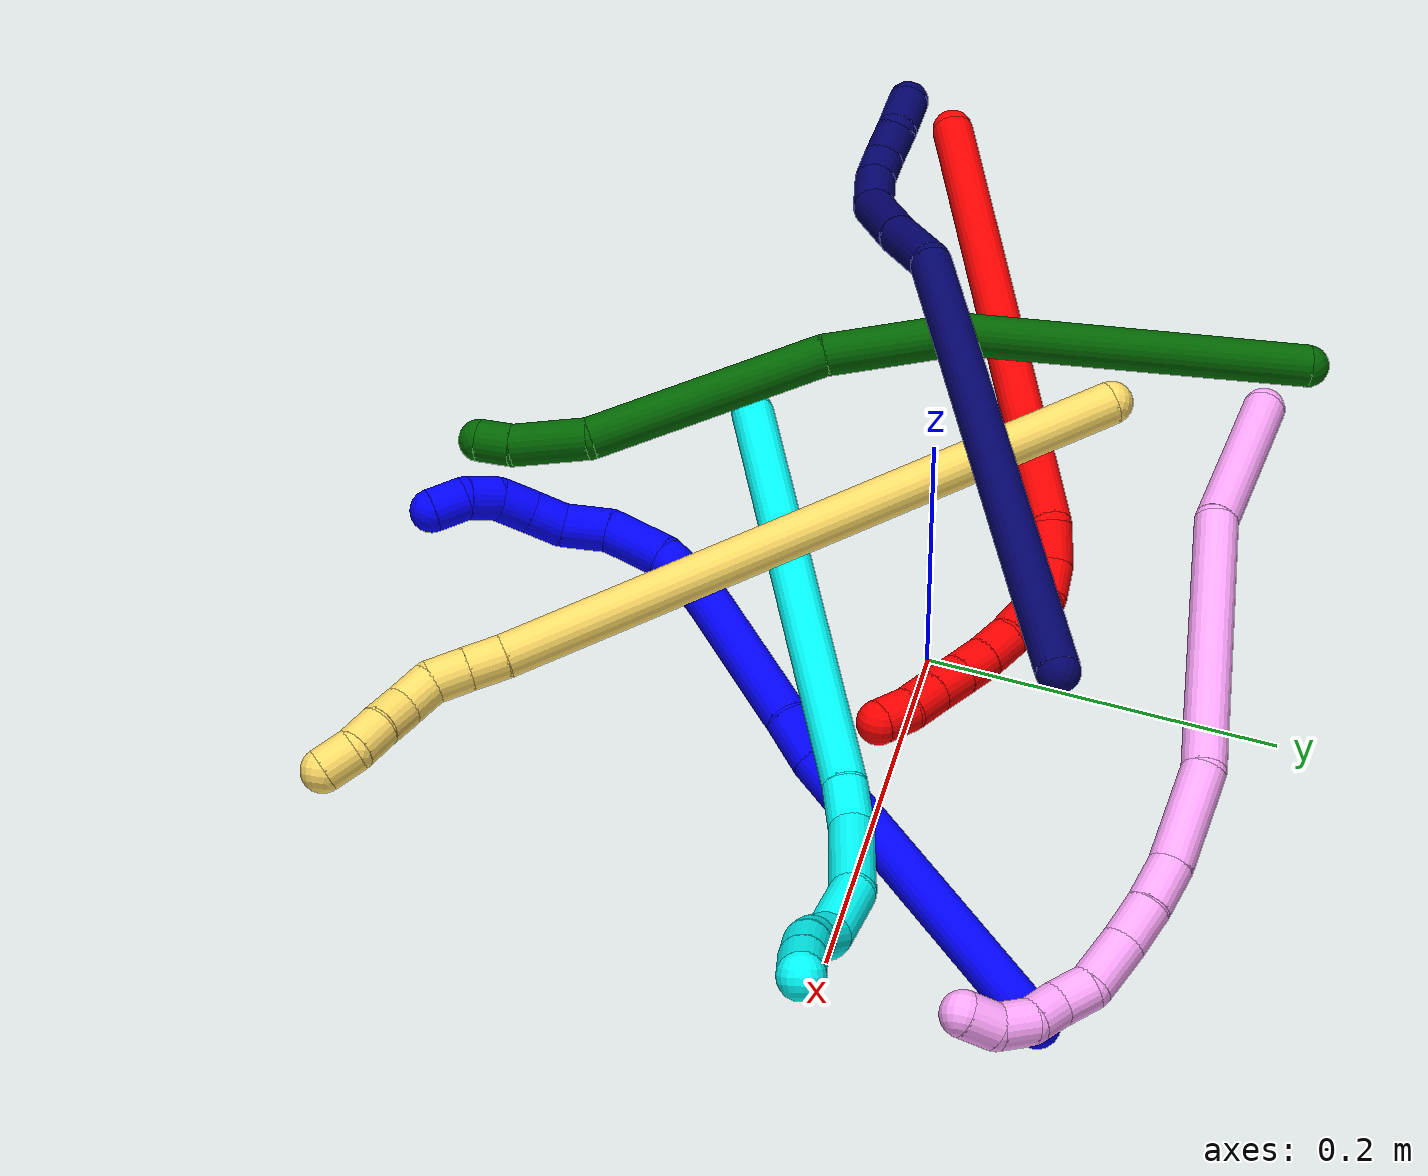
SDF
<sdf version="1.7">
 <world name="default">
  <plugin name="TubeGeneratorPlugin" filename="libtube_generator_plugin.so"/>
  <model name="photoneo_s_sensor">
   <static>1</static>
   <pose>0 0 2 1.57079 1.57079 3.14159</pose>
   <link name="link">
    <inertial><mass>0.1</mass></inertial>
    <sensor name="sensor" type="depth">
     <update_rate>30</update_rate>
     <camera>
      <horizontal_fov>1.22</horizontal_fov>
      <image><width>1920</width><height>1200</height><format>B8G8R8</format></image>
      <clip><near>0.1</near><far>4</far></clip>
      <depth_camera><output>points</output></depth_camera>
     </camera>
     <plugin name="camera_plugin" filename="libgazebo_ros_depth_camera.so">
      <baseline>0.2</baseline>
      <alwaysOn>1</alwaysOn>
      <updateRate>0.0</updateRate>
      <cameraName>camera_ir</cameraName>
      <imageTopicName>/camera/color/image_raw</imageTopicName>
      <cameraInfoTopicName>/camera/color/camera_info</cameraInfoTopicName>
      <depthImageTopicName>/camera/depth/image_raw</depthImageTopicName>
      <depthImageCameraInfoTopicName>/camera/depth/camera_info</depthImageCameraInfoTopicName>
      <pointCloudTopicName>/camera/depth/points</pointCloudTopicName>
      <frameName>fr_optical</frameName>
      <pointCloudCutoff>0.1</pointCloudCutoff>
      <pointCloudCutoffMax>2.0</pointCloudCutoffMax>
      <distortionK1>0</distortionK1>
      <distortionK2>0</distortionK2>
      <distortionK3>0</distortionK3>
      <distortionT1>0</distortionT1>
      <distortionT2>0</distortionT2>
      <CxPrime>0</CxPrime>
      <Cx>0</Cx>
      <Cy>0</Cy>
      <focalLength>0</focalLength>
      <hackBaseline>0</hackBaseline>
     </plugin>
    </sensor>
   </link>
  </model>
  <gravity>0 0 -9.8</gravity>
  <magnetic_field>6e-06 2.3e-05 -4.2e-05</magnetic_field>
  <atmosphere type="adiabatic"/>
  <physics name="default_physics" default="0" type="ode">
   <max_step_size>0.003</max_step_size>
   <real_time_factor>1</real_time_factor>
   <real_time_update_rate>1000</real_time_update_rate>
   <max_contacts>10000</max_contacts>
   <ode>
    <solver>
     <type>quick</type>
     <iters>100</iters>
     <sor>1.3</sor>
     <use_dynamic_moi_rescaling>0</use_dynamic_moi_rescaling>
    </solver>
    <constraints>
     <contact_max_correcting_vel>0</contact_max_correcting_vel>
     <contact_surface_layer>0.001</contact_surface_layer>
     <cfm>0</cfm>
     <erp>0.2</erp>
    </constraints>
   </ode>
  </physics>
  <scene><ambient>0.4 0.4 0.4 1</ambient><background>0.7 0.7 0.7 1</background><shadows>0</shadows></scene>
  <audio><device>default</device></audio>
  <spherical_coordinates>
   <surface_model>EARTH_WGS84</surface_model>
   <latitude_deg>0</latitude_deg>
   <longitude_deg>0</longitude_deg>
   <elevation>0</elevation>
   <heading_deg>0</heading_deg>
  </spherical_coordinates>
  <model name="bin">
   <static>1</static>
   <link name="bottom">
    <collision name="collision-bottom">
     <pose>0 0 -0.01 0 -0 0</pose>
     <geometry><box><size>0.8 0.6 0.02</size></box></geometry>
     <surface>
      <friction><ode><mu>100</mu><mu2>100</mu2></ode></friction>
      <contact><collide_bitmask>65535</collide_bitmask></contact>
     </surface>
    </collision>
   </link>
   <link name="west_wall">
    <collision name="collision-west_wall">
     <pose>-0.41 0 0.1 0 -0 0</pose>
     <geometry><box><size>0.02 0.6 0.2</size></box></geometry>
     <surface>
      <friction><ode><mu>100</mu><mu2>100</mu2></ode></friction>
      <contact><collide_bitmask>65535</collide_bitmask></contact>
     </surface>
    </collision>
   </link>
   <link name="east_wall">
    <collision name="collision-east_wall">
     <pose>0.41 0 0.1 0 -0 0</pose>
     <geometry><box><size>0.02 0.6 0.2</size></box></geometry>
     <surface>
      <friction><ode><mu>100</mu><mu2>100</mu2></ode></friction>
      <contact><collide_bitmask>65535</collide_bitmask></contact>
     </surface>
    </collision>
   </link>
   <link name="south_wall">
    <collision name="collision-south_wall">
     <pose>0 -0.31 0.1 0 -0 0</pose>
     <geometry><box><size>0.8 0.02 0.2</size></box></geometry>
     <surface>
      <friction><ode><mu>100</mu><mu2>100</mu2></ode></friction>
      <contact><collide_bitmask>65535</collide_bitmask></contact>
     </surface>
    </collision>
   </link>
   <link name="north_wall">
    <collision name="collision-north_wall">
     <pose>0 0.31 0.1 0 -0 0</pose>
     <geometry><box><size>0.8 0.02 0.2</size></box></geometry>
     <surface>
      <friction><ode><mu>100</mu><mu2>100</mu2></ode></friction>
      <contact><collide_bitmask>65535</collide_bitmask></contact>
     </surface>
    </collision>
   </link>
  </model>
  <model name="1">
   <static>0</static>
   <link name="1">
    <collision name="collision-cylinder-e_1_1_4">
     <pose>-0.047788 -0.061187 0.062227 0.776971 -0.50099 -0.208687</pose>
     <geometry><cylinder><radius>0.0125</radius><length>0.198995</length></cylinder></geometry>
     <surface>
      <friction><ode><mu>1.16</mu><mu2>1.16</mu2><slip1>0</slip1><slip2>0</slip2></ode></friction>
      <contact><ode><kp>1e+06</kp><kd>1</kd><max_vel>0</max_vel><min_depth>0.001</min_depth></ode></contact>
     </surface>
    </collision>
    <visual name="visual-cylinder-e_1_1_4">
     <pose>-0.047788 -0.061187 0.062227 0.776971 -0.50099 -0.208687</pose>
     <geometry><cylinder><radius>0.0125</radius><length>0.198995</length></cylinder></geometry>
     <material><ambient>0 0 1 1</ambient></material>
    </visual>
    <collision name="collision-cylinder-e_2_4_5">
     <pose>-0.10465 -0.129937 0.133306 0.706986 -0.662027 -0.252267</pose>
     <geometry><cylinder><radius>0.0125</radius><length>0.029522</length></cylinder></geometry>
     <surface>
      <friction><ode><mu>1.16</mu><mu2>1.16</mu2><slip1>0</slip1><slip2>0</slip2></ode></friction>
      <contact><ode><kp>1e+06</kp><kd>1</kd><max_vel>0</max_vel><min_depth>0.001</min_depth></ode></contact>
     </surface>
    </collision>
    <visual name="visual-cylinder-e_2_4_5">
     <pose>-0.10465 -0.129937 0.133306 0.706986 -0.662027 -0.252267</pose>
     <geometry><cylinder><radius>0.0125</radius><length>0.029522</length></cylinder></geometry>
     <material><ambient>0 0 1 1</ambient></material>
    </visual>
    <collision name="collision-cylinder-e_3_5_6">
     <pose>-0.139918 -0.167301 0.168571 0.845625 -0.581835 -0.267829</pose>
     <geometry><cylinder><radius>0.0125</radius><length>0.095329</length></cylinder></geometry>
     <surface>
      <friction><ode><mu>1.16</mu><mu2>1.16</mu2><slip1>0</slip1><slip2>0</slip2></ode></friction>
      <contact><ode><kp>1e+06</kp><kd>1</kd><max_vel>0</max_vel><min_depth>0.001</min_depth></ode></contact>
     </surface>
    </collision>
    <visual name="visual-cylinder-e_3_5_6">
     <pose>-0.139918 -0.167301 0.168571 0.845625 -0.581835 -0.267829</pose>
     <geometry><cylinder><radius>0.0125</radius><length>0.095329</length></cylinder></geometry>
     <material><ambient>0 0 1 1</ambient></material>
    </visual>
    <collision name="collision-cylinder-e_4_6_7">
     <pose>-0.17296 -0.205547 0.206789 0.6209 -0.440771 -0.143498</pose>
     <geometry><cylinder><radius>0.0125</radius><length>0.032099</length></cylinder></geometry>
     <surface>
      <friction><ode><mu>1.16</mu><mu2>1.16</mu2><slip1>0</slip1><slip2>0</slip2></ode></friction>
      <contact><ode><kp>1e+06</kp><kd>1</kd><max_vel>0</max_vel><min_depth>0.001</min_depth></ode></contact>
     </surface>
    </collision>
    <visual name="visual-cylinder-e_4_6_7">
     <pose>-0.17296 -0.205547 0.206789 0.6209 -0.440771 -0.143498</pose>
     <geometry><cylinder><radius>0.0125</radius><length>0.032099</length></cylinder></geometry>
     <material><ambient>0 0 1 1</ambient></material>
    </visual>
    <collision name="collision-cylinder-e_5_7_8">
     <pose>-0.182795 -0.222759 0.234167 0.512783 -0.165665 -0.043524</pose>
     <geometry><cylinder><radius>0.0125</radius><length>0.036236</length></cylinder></geometry>
     <surface>
      <friction><ode><mu>1.16</mu><mu2>1.16</mu2><slip1>0</slip1><slip2>0</slip2></ode></friction>
      <contact><ode><kp>1e+06</kp><kd>1</kd><max_vel>0</max_vel><min_depth>0.001</min_depth></ode></contact>
     </surface>
    </collision>
    <visual name="visual-cylinder-e_5_7_8">
     <pose>-0.182795 -0.222759 0.234167 0.512783 -0.165665 -0.043524</pose>
     <geometry><cylinder><radius>0.0125</radius><length>0.036236</length></cylinder></geometry>
     <material><ambient>0 0 1 1</ambient></material>
    </visual>
    <collision name="collision-cylinder-e_6_8_9">
     <pose>-0.183669 -0.234596 0.26282 0.230466 0.15606 0.0181</pose>
     <geometry><cylinder><radius>0.0125</radius><length>0.027203</length></cylinder></geometry>
     <surface>
      <friction><ode><mu>1.16</mu><mu2>1.16</mu2><slip1>0</slip1><slip2>0</slip2></ode></friction>
      <contact><ode><kp>1e+06</kp><kd>1</kd><max_vel>0</max_vel><min_depth>0.001</min_depth></ode></contact>
     </surface>
    </collision>
    <visual name="visual-cylinder-e_6_8_9">
     <pose>-0.183669 -0.234596 0.26282 0.230466 0.15606 0.0181</pose>
     <geometry><cylinder><radius>0.0125</radius><length>0.027203</length></cylinder></geometry>
     <material><ambient>0 0 1 1</ambient></material>
    </visual>
    <collision name="collision-cylinder-e_7_9_10">
     <pose>-0.182825 -0.237369 0.285985 -0.029342 -0.125291 0.001841</pose>
     <geometry><cylinder><radius>0.0125</radius><length>0.020337</length></cylinder></geometry>
     <surface>
      <friction><ode><mu>1.16</mu><mu2>1.16</mu2><slip1>0</slip1><slip2>0</slip2></ode></friction>
      <contact><ode><kp>1e+06</kp><kd>1</kd><max_vel>0</max_vel><min_depth>0.001</min_depth></ode></contact>
     </surface>
    </collision>
    <visual name="visual-cylinder-e_7_9_10">
     <pose>-0.182825 -0.237369 0.285985 -0.029342 -0.125291 0.001841</pose>
     <geometry><cylinder><radius>0.0125</radius><length>0.020337</length></cylinder></geometry>
     <material><ambient>0 0 1 1</ambient></material>
    </visual>
    <collision name="collision-cylinder-e_8_10_11">
     <pose>-0.185231 -0.235917 0.306025 -0.115547 -0.112752 0.006528</pose>
     <geometry><cylinder><radius>0.0125</radius><length>0.020174</length></cylinder></geometry>
     <surface>
      <friction><ode><mu>1.16</mu><mu2>1.16</mu2><slip1>0</slip1><slip2>0</slip2></ode></friction>
      <contact><ode><kp>1e+06</kp><kd>1</kd><max_vel>0</max_vel><min_depth>0.001</min_depth></ode></contact>
     </surface>
    </collision>
    <visual name="visual-cylinder-e_8_10_11">
     <pose>-0.185231 -0.235917 0.306025 -0.115547 -0.112752 0.006528</pose>
     <geometry><cylinder><radius>0.0125</radius><length>0.020174</length></cylinder></geometry>
     <material><ambient>0 0 1 1</ambient></material>
    </visual>
    <collision name="collision-cylinder-e_9_11_12">
     <pose>-0.184079 -0.231832 0.325308 -0.304399 0.229833 -0.035405</pose>
     <geometry><cylinder><radius>0.0125</radius><length>0.020081</length></cylinder></geometry>
     <surface>
      <friction><ode><mu>1.16</mu><mu2>1.16</mu2><slip1>0</slip1><slip2>0</slip2></ode></friction>
      <contact><ode><kp>1e+06</kp><kd>1</kd><max_vel>0</max_vel><min_depth>0.001</min_depth></ode></contact>
     </surface>
    </collision>
    <visual name="visual-cylinder-e_9_11_12">
     <pose>-0.184079 -0.231832 0.325308 -0.304399 0.229833 -0.035405</pose>
     <geometry><cylinder><radius>0.0125</radius><length>0.020081</length></cylinder></geometry>
     <material><ambient>0 0 1 1</ambient></material>
    </visual>
    <collision name="collision-cylinder-e_10_12_2">
     <pose>-0.176008 -0.228151 0.342774 -0.09191 0.615872 -0.029251</pose>
     <geometry><cylinder><radius>0.0125</radius><length>0.020024</length></cylinder></geometry>
     <surface>
      <friction><ode><mu>1.16</mu><mu2>1.16</mu2><slip1>0</slip1><slip2>0</slip2></ode></friction>
      <contact><ode><kp>1e+06</kp><kd>1</kd><max_vel>0</max_vel><min_depth>0.001</min_depth></ode></contact>
     </surface>
    </collision>
    <visual name="visual-cylinder-e_10_12_2">
     <pose>-0.176008 -0.228151 0.342774 -0.09191 0.615872 -0.029251</pose>
     <geometry><cylinder><radius>0.0125</radius><length>0.020024</length></cylinder></geometry>
     <material><ambient>0 0 1 1</ambient></material>
    </visual>
    <collision name="collision-sphere-2">
     <pose>-0.170224 -0.227401 0.350912 0 -0 0</pose>
     <geometry><sphere><radius>0.0125</radius></sphere></geometry>
     <surface>
      <friction><ode><mu>1.16</mu><mu2>1.16</mu2><slip1>0</slip1><slip2>0</slip2></ode></friction>
      <contact><ode><kp>1e+06</kp><kd>1</kd><max_vel>0</max_vel><min_depth>0.001</min_depth></ode></contact>
     </surface>
    </collision>
    <visual name="visual-sphere-2">
     <pose>-0.170224 -0.227401 0.350912 0 -0 0</pose>
     <geometry><sphere><radius>0.0125</radius></sphere></geometry>
     <material><ambient>0 0 1 1</ambient></material>
    </visual>
    <collision name="collision-sphere-12">
     <pose>-0.181791 -0.228901 0.334635 0 -0 0</pose>
     <geometry><sphere><radius>0.0125</radius></sphere></geometry>
     <surface>
      <friction><ode><mu>1.16</mu><mu2>1.16</mu2><slip1>0</slip1><slip2>0</slip2></ode></friction>
      <contact><ode><kp>1e+06</kp><kd>1</kd><max_vel>0</max_vel><min_depth>0.001</min_depth></ode></contact>
     </surface>
    </collision>
    <visual name="visual-sphere-12">
     <pose>-0.181791 -0.228901 0.334635 0 -0 0</pose>
     <geometry><sphere><radius>0.0125</radius></sphere></geometry>
     <material><ambient>0 0 1 1</ambient></material>
    </visual>
    <collision name="collision-sphere-11">
     <pose>-0.186366 -0.234762 0.315982 0 -0 0</pose>
     <geometry><sphere><radius>0.0125</radius></sphere></geometry>
     <surface>
      <friction><ode><mu>1.16</mu><mu2>1.16</mu2><slip1>0</slip1><slip2>0</slip2></ode></friction>
      <contact><ode><kp>1e+06</kp><kd>1</kd><max_vel>0</max_vel><min_depth>0.001</min_depth></ode></contact>
     </surface>
    </collision>
    <visual name="visual-sphere-11">
     <pose>-0.186366 -0.234762 0.315982 0 -0 0</pose>
     <geometry><sphere><radius>0.0125</radius></sphere></geometry>
     <material><ambient>0 0 1 1</ambient></material>
    </visual>
    <collision name="collision-sphere-10">
     <pose>-0.184096 -0.237073 0.296069 0 -0 0</pose>
     <geometry><sphere><radius>0.0125</radius></sphere></geometry>
     <surface>
      <friction><ode><mu>1.16</mu><mu2>1.16</mu2><slip1>0</slip1><slip2>0</slip2></ode></friction>
      <contact><ode><kp>1e+06</kp><kd>1</kd><max_vel>0</max_vel><min_depth>0.001</min_depth></ode></contact>
     </surface>
    </collision>
    <visual name="visual-sphere-10">
     <pose>-0.184096 -0.237073 0.296069 0 -0 0</pose>
     <geometry><sphere><radius>0.0125</radius></sphere></geometry>
     <material><ambient>0 0 1 1</ambient></material>
    </visual>
    <collision name="collision-sphere-9">
     <pose>-0.181555 -0.237665 0.275901 0 -0 0</pose>
     <geometry><sphere><radius>0.0125</radius></sphere></geometry>
     <surface>
      <friction><ode><mu>1.16</mu><mu2>1.16</mu2><slip1>0</slip1><slip2>0</slip2></ode></friction>
      <contact><ode><kp>1e+06</kp><kd>1</kd><max_vel>0</max_vel><min_depth>0.001</min_depth></ode></contact>
     </surface>
    </collision>
    <visual name="visual-sphere-9">
     <pose>-0.181555 -0.237665 0.275901 0 -0 0</pose>
     <geometry><sphere><radius>0.0125</radius></sphere></geometry>
     <material><ambient>0 0 1 1</ambient></material>
    </visual>
    <collision name="collision-sphere-4">
     <pose>-0.095576 -0.122374 0.124454 0 -0 0</pose>
     <geometry><sphere><radius>0.0125</radius></sphere></geometry>
     <surface>
      <friction><ode><mu>1.16</mu><mu2>1.16</mu2><slip1>0</slip1><slip2>0</slip2></ode></friction>
      <contact><ode><kp>1e+06</kp><kd>1</kd><max_vel>0</max_vel><min_depth>0.001</min_depth></ode></contact>
     </surface>
    </collision>
    <visual name="visual-sphere-4">
     <pose>-0.095576 -0.122374 0.124454 0 -0 0</pose>
     <geometry><sphere><radius>0.0125</radius></sphere></geometry>
     <material><ambient>0 0 1 1</ambient></material>
    </visual>
    <collision name="collision-sphere-1">
     <geometry><sphere><radius>0.0125</radius></sphere></geometry>
     <surface>
      <friction><ode><mu>1.16</mu><mu2>1.16</mu2><slip1>0</slip1><slip2>0</slip2></ode></friction>
      <contact><ode><kp>1e+06</kp><kd>1</kd><max_vel>0</max_vel><min_depth>0.001</min_depth></ode></contact>
     </surface>
    </collision>
    <visual name="visual-sphere-1">
     <geometry><sphere><radius>0.0125</radius></sphere></geometry>
     <material><ambient>0 0 1 1</ambient></material>
    </visual>
    <collision name="collision-sphere-8">
     <pose>-0.185783 -0.231526 0.249739 0 -0 0</pose>
     <geometry><sphere><radius>0.0125</radius></sphere></geometry>
     <surface>
      <friction><ode><mu>1.16</mu><mu2>1.16</mu2><slip1>0</slip1><slip2>0</slip2></ode></friction>
      <contact><ode><kp>1e+06</kp><kd>1</kd><max_vel>0</max_vel><min_depth>0.001</min_depth></ode></contact>
     </surface>
    </collision>
    <visual name="visual-sphere-8">
     <pose>-0.185783 -0.231526 0.249739 0 -0 0</pose>
     <geometry><sphere><radius>0.0125</radius></sphere></geometry>
     <material><ambient>0 0 1 1</ambient></material>
    </visual>
    <collision name="collision-sphere-5">
     <pose>-0.113724 -0.137499 0.142159 0 -0 0</pose>
     <geometry><sphere><radius>0.0125</radius></sphere></geometry>
     <surface>
      <friction><ode><mu>1.16</mu><mu2>1.16</mu2><slip1>0</slip1><slip2>0</slip2></ode></friction>
      <contact><ode><kp>1e+06</kp><kd>1</kd><max_vel>0</max_vel><min_depth>0.001</min_depth></ode></contact>
     </surface>
    </collision>
    <visual name="visual-sphere-5">
     <pose>-0.113724 -0.137499 0.142159 0 -0 0</pose>
     <geometry><sphere><radius>0.0125</radius></sphere></geometry>
     <material><ambient>0 0 1 1</ambient></material>
    </visual>
    <collision name="collision-sphere-6">
     <pose>-0.166113 -0.197103 0.194983 0 -0 0</pose>
     <geometry><sphere><radius>0.0125</radius></sphere></geometry>
     <surface>
      <friction><ode><mu>1.16</mu><mu2>1.16</mu2><slip1>0</slip1><slip2>0</slip2></ode></friction>
      <contact><ode><kp>1e+06</kp><kd>1</kd><max_vel>0</max_vel><min_depth>0.001</min_depth></ode></contact>
     </surface>
    </collision>
    <visual name="visual-sphere-6">
     <pose>-0.166113 -0.197103 0.194983 0 -0 0</pose>
     <geometry><sphere><radius>0.0125</radius></sphere></geometry>
     <material><ambient>0 0 1 1</ambient></material>
    </visual>
    <collision name="collision-sphere-7">
     <pose>-0.179807 -0.213992 0.218595 0 -0 0</pose>
     <geometry><sphere><radius>0.0125</radius></sphere></geometry>
     <surface>
      <friction><ode><mu>1.16</mu><mu2>1.16</mu2><slip1>0</slip1><slip2>0</slip2></ode></friction>
      <contact><ode><kp>1e+06</kp><kd>1</kd><max_vel>0</max_vel><min_depth>0.001</min_depth></ode></contact>
     </surface>
    </collision>
    <visual name="visual-sphere-7">
     <pose>-0.179807 -0.213992 0.218595 0 -0 0</pose>
     <geometry><sphere><radius>0.0125</radius></sphere></geometry>
     <material><ambient>0 0 1 1</ambient></material>
    </visual>
    <inertial>
     <pose>-0.11557 -0.143645 0.160093 0 -0 0</pose>
     <mass>0.5</mass>
     <inertia>
      <ixx>0.000499</ixx>
      <ixy>0</ixy>
      <ixz>0</ixz>
      <iyy>0.000429</iyy>
      <iyz>0</iyz>
      <izz>0.000854</izz>
     </inertia>
    </inertial>
   </link>
   <pose>0.209703 0.117588 0.011491 1.16838 0.589043 -0.040525</pose>
  </model>
  <model name="2">
   <static>0</static>
   <link name="2">
    <collision name="collision-cylinder-e_1_1_4">
     <pose>0.132969 0.051618 -0.06299 -2.4551 1.02127 -2.00582</pose>
     <geometry><cylinder><radius>0.0125</radius><length>0.311853</length></cylinder></geometry>
     <surface>
      <friction><ode><mu>1.16</mu><mu2>1.16</mu2><slip1>0</slip1><slip2>0</slip2></ode></friction>
      <contact><ode><kp>1e+06</kp><kd>1</kd><max_vel>0</max_vel><min_depth>0.001</min_depth></ode></contact>
     </surface>
    </collision>
    <visual name="visual-cylinder-e_1_1_4">
     <pose>0.132969 0.051618 -0.06299 -2.4551 1.02127 -2.00582</pose>
     <geometry><cylinder><radius>0.0125</radius><length>0.311853</length></cylinder></geometry>
     <material><ambient>1 0 0 1</ambient></material>
    </visual>
    <collision name="collision-cylinder-e_2_4_5">
     <pose>0.273718 0.105488 -0.134866 -2.89342 0.703719 -2.4866</pose>
     <geometry><cylinder><radius>0.0125</radius><length>0.024045</length></cylinder></geometry>
     <surface>
      <friction><ode><mu>1.16</mu><mu2>1.16</mu2><slip1>0</slip1><slip2>0</slip2></ode></friction>
      <contact><ode><kp>1e+06</kp><kd>1</kd><max_vel>0</max_vel><min_depth>0.001</min_depth></ode></contact>
     </surface>
    </collision>
    <visual name="visual-cylinder-e_2_4_5">
     <pose>0.273718 0.105488 -0.134866 -2.89342 0.703719 -2.4866</pose>
     <geometry><cylinder><radius>0.0125</radius><length>0.024045</length></cylinder></geometry>
     <material><ambient>1 0 0 1</ambient></material>
    </visual>
    <collision name="collision-cylinder-e_3_5_6">
     <pose>0.290549 0.107527 -0.149459 3.10449 1.00794 3.07434</pose>
     <geometry><cylinder><radius>0.0125</radius><length>0.021407</length></cylinder></geometry>
     <surface>
      <friction><ode><mu>1.16</mu><mu2>1.16</mu2><slip1>0</slip1><slip2>0</slip2></ode></friction>
      <contact><ode><kp>1e+06</kp><kd>1</kd><max_vel>0</max_vel><min_depth>0.001</min_depth></ode></contact>
     </surface>
    </collision>
    <visual name="visual-cylinder-e_3_5_6">
     <pose>0.290549 0.107527 -0.149459 3.10449 1.00794 3.07434</pose>
     <geometry><cylinder><radius>0.0125</radius><length>0.021407</length></cylinder></geometry>
     <material><ambient>1 0 0 1</ambient></material>
    </visual>
    <collision name="collision-cylinder-e_4_6_7">
     <pose>0.308315 0.102963 -0.158263 2.18926 1.0209 1.65293</pose>
     <geometry><cylinder><radius>0.0125</radius><length>0.020441</length></cylinder></geometry>
     <surface>
      <friction><ode><mu>1.16</mu><mu2>1.16</mu2><slip1>0</slip1><slip2>0</slip2></ode></friction>
      <contact><ode><kp>1e+06</kp><kd>1</kd><max_vel>0</max_vel><min_depth>0.001</min_depth></ode></contact>
     </surface>
    </collision>
    <visual name="visual-cylinder-e_4_6_7">
     <pose>0.308315 0.102963 -0.158263 2.18926 1.0209 1.65293</pose>
     <geometry><cylinder><radius>0.0125</radius><length>0.020441</length></cylinder></geometry>
     <material><ambient>1 0 0 1</ambient></material>
    </visual>
    <collision name="collision-cylinder-e_5_7_8">
     <pose>0.326481 0.094724 -0.162981 1.96564 1.15161 1.54429</pose>
     <geometry><cylinder><radius>0.0125</radius><length>0.020697</length></cylinder></geometry>
     <surface>
      <friction><ode><mu>1.16</mu><mu2>1.16</mu2><slip1>0</slip1><slip2>0</slip2></ode></friction>
      <contact><ode><kp>1e+06</kp><kd>1</kd><max_vel>0</max_vel><min_depth>0.001</min_depth></ode></contact>
     </surface>
    </collision>
    <visual name="visual-cylinder-e_5_7_8">
     <pose>0.326481 0.094724 -0.162981 1.96564 1.15161 1.54429</pose>
     <geometry><cylinder><radius>0.0125</radius><length>0.020697</length></cylinder></geometry>
     <material><ambient>1 0 0 1</ambient></material>
    </visual>
    <collision name="collision-cylinder-e_6_8_9">
     <pose>0.34433 0.085446 -0.167579 2.07566 0.938046 1.4194</pose>
     <geometry><cylinder><radius>0.0125</radius><length>0.020825</length></cylinder></geometry>
     <surface>
      <friction><ode><mu>1.16</mu><mu2>1.16</mu2><slip1>0</slip1><slip2>0</slip2></ode></friction>
      <contact><ode><kp>1e+06</kp><kd>1</kd><max_vel>0</max_vel><min_depth>0.001</min_depth></ode></contact>
     </surface>
    </collision>
    <visual name="visual-cylinder-e_6_8_9">
     <pose>0.34433 0.085446 -0.167579 2.07566 0.938046 1.4194</pose>
     <geometry><cylinder><radius>0.0125</radius><length>0.020825</length></cylinder></geometry>
     <material><ambient>1 0 0 1</ambient></material>
    </visual>
    <collision name="collision-cylinder-e_7_9_10">
     <pose>0.360692 0.074248 -0.172739 1.9301 0.908984 1.22877</pose>
     <geometry><cylinder><radius>0.0125</radius><length>0.020193</length></cylinder></geometry>
     <surface>
      <friction><ode><mu>1.16</mu><mu2>1.16</mu2><slip1>0</slip1><slip2>0</slip2></ode></friction>
      <contact><ode><kp>1e+06</kp><kd>1</kd><max_vel>0</max_vel><min_depth>0.001</min_depth></ode></contact>
     </surface>
    </collision>
    <visual name="visual-cylinder-e_7_9_10">
     <pose>0.360692 0.074248 -0.172739 1.9301 0.908984 1.22877</pose>
     <geometry><cylinder><radius>0.0125</radius><length>0.020193</length></cylinder></geometry>
     <material><ambient>1 0 0 1</ambient></material>
    </visual>
    <collision name="collision-cylinder-e_8_10_11">
     <pose>0.37674 0.062513 -0.176993 1.90713 0.9104 1.20752</pose>
     <geometry><cylinder><radius>0.0125</radius><length>0.020469</length></cylinder></geometry>
     <surface>
      <friction><ode><mu>1.16</mu><mu2>1.16</mu2><slip1>0</slip1><slip2>0</slip2></ode></friction>
      <contact><ode><kp>1e+06</kp><kd>1</kd><max_vel>0</max_vel><min_depth>0.001</min_depth></ode></contact>
     </surface>
    </collision>
    <visual name="visual-cylinder-e_8_10_11">
     <pose>0.37674 0.062513 -0.176993 1.90713 0.9104 1.20752</pose>
     <geometry><cylinder><radius>0.0125</radius><length>0.020469</length></cylinder></geometry>
     <material><ambient>1 0 0 1</ambient></material>
    </visual>
    <collision name="collision-cylinder-e_9_11_12">
     <pose>0.392946 0.051039 -0.181037 1.91227 0.943582 1.25175</pose>
     <geometry><cylinder><radius>0.0125</radius><length>0.020067</length></cylinder></geometry>
     <surface>
      <friction><ode><mu>1.16</mu><mu2>1.16</mu2><slip1>0</slip1><slip2>0</slip2></ode></friction>
      <contact><ode><kp>1e+06</kp><kd>1</kd><max_vel>0</max_vel><min_depth>0.001</min_depth></ode></contact>
     </surface>
    </collision>
    <visual name="visual-cylinder-e_9_11_12">
     <pose>0.392946 0.051039 -0.181037 1.91227 0.943582 1.25175</pose>
     <geometry><cylinder><radius>0.0125</radius><length>0.020067</length></cylinder></geometry>
     <material><ambient>1 0 0 1</ambient></material>
    </visual>
    <collision name="collision-cylinder-e_10_12_2">
     <pose>0.408021 0.038451 -0.184481 1.77692 0.768407 0.923407</pose>
     <geometry><cylinder><radius>0.0125</radius><length>0.020004</length></cylinder></geometry>
     <surface>
      <friction><ode><mu>1.16</mu><mu2>1.16</mu2><slip1>0</slip1><slip2>0</slip2></ode></friction>
      <contact><ode><kp>1e+06</kp><kd>1</kd><max_vel>0</max_vel><min_depth>0.001</min_depth></ode></contact>
     </surface>
    </collision>
    <visual name="visual-cylinder-e_10_12_2">
     <pose>0.408021 0.038451 -0.184481 1.77692 0.768407 0.923407</pose>
     <geometry><cylinder><radius>0.0125</radius><length>0.020004</length></cylinder></geometry>
     <material><ambient>1 0 0 1</ambient></material>
    </visual>
    <collision name="collision-sphere-2">
     <pose>0.414972 0.031411 -0.185952 0 -0 0</pose>
     <geometry><sphere><radius>0.0125</radius></sphere></geometry>
     <surface>
      <friction><ode><mu>1.16</mu><mu2>1.16</mu2><slip1>0</slip1><slip2>0</slip2></ode></friction>
      <contact><ode><kp>1e+06</kp><kd>1</kd><max_vel>0</max_vel><min_depth>0.001</min_depth></ode></contact>
     </surface>
    </collision>
    <visual name="visual-sphere-2">
     <pose>0.414972 0.031411 -0.185952 0 -0 0</pose>
     <geometry><sphere><radius>0.0125</radius></sphere></geometry>
     <material><ambient>1 0 0 1</ambient></material>
    </visual>
    <collision name="collision-sphere-12">
     <pose>0.401069 0.04549 -0.183009 0 -0 0</pose>
     <geometry><sphere><radius>0.0125</radius></sphere></geometry>
     <surface>
      <friction><ode><mu>1.16</mu><mu2>1.16</mu2><slip1>0</slip1><slip2>0</slip2></ode></friction>
      <contact><ode><kp>1e+06</kp><kd>1</kd><max_vel>0</max_vel><min_depth>0.001</min_depth></ode></contact>
     </surface>
    </collision>
    <visual name="visual-sphere-12">
     <pose>0.401069 0.04549 -0.183009 0 -0 0</pose>
     <geometry><sphere><radius>0.0125</radius></sphere></geometry>
     <material><ambient>1 0 0 1</ambient></material>
    </visual>
    <collision name="collision-sphere-11">
     <pose>0.384822 0.056587 -0.179065 0 -0 0</pose>
     <geometry><sphere><radius>0.0125</radius></sphere></geometry>
     <surface>
      <friction><ode><mu>1.16</mu><mu2>1.16</mu2><slip1>0</slip1><slip2>0</slip2></ode></friction>
      <contact><ode><kp>1e+06</kp><kd>1</kd><max_vel>0</max_vel><min_depth>0.001</min_depth></ode></contact>
     </surface>
    </collision>
    <visual name="visual-sphere-11">
     <pose>0.384822 0.056587 -0.179065 0 -0 0</pose>
     <geometry><sphere><radius>0.0125</radius></sphere></geometry>
     <material><ambient>1 0 0 1</ambient></material>
    </visual>
    <collision name="collision-sphere-10">
     <pose>0.368657 0.06844 -0.174921 0 -0 0</pose>
     <geometry><sphere><radius>0.0125</radius></sphere></geometry>
     <surface>
      <friction><ode><mu>1.16</mu><mu2>1.16</mu2><slip1>0</slip1><slip2>0</slip2></ode></friction>
      <contact><ode><kp>1e+06</kp><kd>1</kd><max_vel>0</max_vel><min_depth>0.001</min_depth></ode></contact>
     </surface>
    </collision>
    <visual name="visual-sphere-10">
     <pose>0.368657 0.06844 -0.174921 0 -0 0</pose>
     <geometry><sphere><radius>0.0125</radius></sphere></geometry>
     <material><ambient>1 0 0 1</ambient></material>
    </visual>
    <collision name="collision-sphere-9">
     <pose>0.352727 0.080057 -0.170557 0 -0 0</pose>
     <geometry><sphere><radius>0.0125</radius></sphere></geometry>
     <surface>
      <friction><ode><mu>1.16</mu><mu2>1.16</mu2><slip1>0</slip1><slip2>0</slip2></ode></friction>
      <contact><ode><kp>1e+06</kp><kd>1</kd><max_vel>0</max_vel><min_depth>0.001</min_depth></ode></contact>
     </surface>
    </collision>
    <visual name="visual-sphere-9">
     <pose>0.352727 0.080057 -0.170557 0 -0 0</pose>
     <geometry><sphere><radius>0.0125</radius></sphere></geometry>
     <material><ambient>1 0 0 1</ambient></material>
    </visual>
    <collision name="collision-sphere-4">
     <pose>0.265938 0.103236 -0.125981 0 -0 0</pose>
     <geometry><sphere><radius>0.0125</radius></sphere></geometry>
     <surface>
      <friction><ode><mu>1.16</mu><mu2>1.16</mu2><slip1>0</slip1><slip2>0</slip2></ode></friction>
      <contact><ode><kp>1e+06</kp><kd>1</kd><max_vel>0</max_vel><min_depth>0.001</min_depth></ode></contact>
     </surface>
    </collision>
    <visual name="visual-sphere-4">
     <pose>0.265938 0.103236 -0.125981 0 -0 0</pose>
     <geometry><sphere><radius>0.0125</radius></sphere></geometry>
     <material><ambient>1 0 0 1</ambient></material>
    </visual>
    <collision name="collision-sphere-1">
     <geometry><sphere><radius>0.0125</radius></sphere></geometry>
     <surface>
      <friction><ode><mu>1.16</mu><mu2>1.16</mu2><slip1>0</slip1><slip2>0</slip2></ode></friction>
      <contact><ode><kp>1e+06</kp><kd>1</kd><max_vel>0</max_vel><min_depth>0.001</min_depth></ode></contact>
     </surface>
    </collision>
    <visual name="visual-sphere-1">
     <geometry><sphere><radius>0.0125</radius></sphere></geometry>
     <material><ambient>1 0 0 1</ambient></material>
    </visual>
    <collision name="collision-sphere-8">
     <pose>0.335934 0.090836 -0.164601 0 -0 0</pose>
     <geometry><sphere><radius>0.0125</radius></sphere></geometry>
     <surface>
      <friction><ode><mu>1.16</mu><mu2>1.16</mu2><slip1>0</slip1><slip2>0</slip2></ode></friction>
      <contact><ode><kp>1e+06</kp><kd>1</kd><max_vel>0</max_vel><min_depth>0.001</min_depth></ode></contact>
     </surface>
    </collision>
    <visual name="visual-sphere-8">
     <pose>0.335934 0.090836 -0.164601 0 -0 0</pose>
     <geometry><sphere><radius>0.0125</radius></sphere></geometry>
     <material><ambient>1 0 0 1</ambient></material>
    </visual>
    <collision name="collision-sphere-5">
     <pose>0.281497 0.107739 -0.143752 0 -0 0</pose>
     <geometry><sphere><radius>0.0125</radius></sphere></geometry>
     <surface>
      <friction><ode><mu>1.16</mu><mu2>1.16</mu2><slip1>0</slip1><slip2>0</slip2></ode></friction>
      <contact><ode><kp>1e+06</kp><kd>1</kd><max_vel>0</max_vel><min_depth>0.001</min_depth></ode></contact>
     </surface>
    </collision>
    <visual name="visual-sphere-5">
     <pose>0.281497 0.107739 -0.143752 0 -0 0</pose>
     <geometry><sphere><radius>0.0125</radius></sphere></geometry>
     <material><ambient>1 0 0 1</ambient></material>
    </visual>
    <collision name="collision-sphere-6">
     <pose>0.299601 0.107315 -0.155167 0 -0 0</pose>
     <geometry><sphere><radius>0.0125</radius></sphere></geometry>
     <surface>
      <friction><ode><mu>1.16</mu><mu2>1.16</mu2><slip1>0</slip1><slip2>0</slip2></ode></friction>
      <contact><ode><kp>1e+06</kp><kd>1</kd><max_vel>0</max_vel><min_depth>0.001</min_depth></ode></contact>
     </surface>
    </collision>
    <visual name="visual-sphere-6">
     <pose>0.299601 0.107315 -0.155167 0 -0 0</pose>
     <geometry><sphere><radius>0.0125</radius></sphere></geometry>
     <material><ambient>1 0 0 1</ambient></material>
    </visual>
    <collision name="collision-sphere-7">
     <pose>0.317029 0.098612 -0.16136 0 -0 0</pose>
     <geometry><sphere><radius>0.0125</radius></sphere></geometry>
     <surface>
      <friction><ode><mu>1.16</mu><mu2>1.16</mu2><slip1>0</slip1><slip2>0</slip2></ode></friction>
      <contact><ode><kp>1e+06</kp><kd>1</kd><max_vel>0</max_vel><min_depth>0.001</min_depth></ode></contact>
     </surface>
    </collision>
    <visual name="visual-sphere-7">
     <pose>0.317029 0.098612 -0.16136 0 -0 0</pose>
     <geometry><sphere><radius>0.0125</radius></sphere></geometry>
     <material><ambient>1 0 0 1</ambient></material>
    </visual>
    <inertial>
     <pose>0.211081 0.062705 -0.101237 0 -0 0</pose>
     <mass>0.5</mass>
     <inertia>
      <ixx>-0.001725</ixx>
      <ixy>0</ixy>
      <ixz>0</ixz>
      <iyy>0.000887</iyy>
      <iyz>0</iyz>
      <izz>-0.003027</izz>
     </inertia>
    </inertial>
   </link>
   <pose>-0.375419 -0.088818 0.011496 -0.03916 -0.488552 0.125887</pose>
  </model>
  <model name="3">
   <static>0</static>
   <link name="3">
    <collision name="collision-cylinder-e_1_1_4">
     <pose>0.07858 0.048587 -0.102745 -2.69987 0.604925 -1.89414</pose>
     <geometry><cylinder><radius>0.0125</radius><length>0.276349</length></cylinder></geometry>
     <surface>
      <friction><ode><mu>1.16</mu><mu2>1.16</mu2><slip1>0</slip1><slip2>0</slip2></ode></friction>
      <contact><ode><kp>1e+06</kp><kd>1</kd><max_vel>0</max_vel><min_depth>0.001</min_depth></ode></contact>
     </surface>
    </collision>
    <visual name="visual-cylinder-e_1_1_4">
     <pose>0.07858 0.048587 -0.102745 -2.69987 0.604925 -1.89414</pose>
     <geometry><cylinder><radius>0.0125</radius><length>0.276349</length></cylinder></geometry>
     <material><ambient>0.003922 1 0.996078 1</ambient></material>
    </visual>
    <collision name="collision-cylinder-e_2_4_5">
     <pose>0.164092 0.100823 -0.216525 -2.8223 0.53783 -2.08406</pose>
     <geometry><cylinder><radius>0.0125</radius><length>0.027064</length></cylinder></geometry>
     <surface>
      <friction><ode><mu>1.16</mu><mu2>1.16</mu2><slip1>0</slip1><slip2>0</slip2></ode></friction>
      <contact><ode><kp>1e+06</kp><kd>1</kd><max_vel>0</max_vel><min_depth>0.001</min_depth></ode></contact>
     </surface>
    </collision>
    <visual name="visual-cylinder-e_2_4_5">
     <pose>0.164092 0.100823 -0.216525 -2.8223 0.53783 -2.08406</pose>
     <geometry><cylinder><radius>0.0125</radius><length>0.027064</length></cylinder></geometry>
     <material><ambient>0.003922 1 0.996078 1</ambient></material>
    </visual>
    <collision name="collision-cylinder-e_3_5_6">
     <pose>0.196277 0.111014 -0.241889 -2.71328 1.01307 -2.3944</pose>
     <geometry><cylinder><radius>0.0125</radius><length>0.059528</length></cylinder></geometry>
     <surface>
      <friction><ode><mu>1.16</mu><mu2>1.16</mu2><slip1>0</slip1><slip2>0</slip2></ode></friction>
      <contact><ode><kp>1e+06</kp><kd>1</kd><max_vel>0</max_vel><min_depth>0.001</min_depth></ode></contact>
     </surface>
    </collision>
    <visual name="visual-cylinder-e_3_5_6">
     <pose>0.196277 0.111014 -0.241889 -2.71328 1.01307 -2.3944</pose>
     <geometry><cylinder><radius>0.0125</radius><length>0.059528</length></cylinder></geometry>
     <material><ambient>0.003922 1 0.996078 1</ambient></material>
    </visual>
    <collision name="collision-cylinder-e_4_6_7">
     <pose>0.238914 0.115432 -0.26568 2.92073 1.06197 2.76836</pose>
     <geometry><cylinder><radius>0.0125</radius><length>0.039809</length></cylinder></geometry>
     <surface>
      <friction><ode><mu>1.16</mu><mu2>1.16</mu2><slip1>0</slip1><slip2>0</slip2></ode></friction>
      <contact><ode><kp>1e+06</kp><kd>1</kd><max_vel>0</max_vel><min_depth>0.001</min_depth></ode></contact>
     </surface>
    </collision>
    <visual name="visual-cylinder-e_4_6_7">
     <pose>0.238914 0.115432 -0.26568 2.92073 1.06197 2.76836</pose>
     <geometry><cylinder><radius>0.0125</radius><length>0.039809</length></cylinder></geometry>
     <material><ambient>0.003922 1 0.996078 1</ambient></material>
    </visual>
    <collision name="collision-cylinder-e_5_7_8">
     <pose>0.267045 0.111657 -0.275149 1.57577 1.41838 1.42329</pose>
     <geometry><cylinder><radius>0.0125</radius><length>0.021749</length></cylinder></geometry>
     <surface>
      <friction><ode><mu>1.16</mu><mu2>1.16</mu2><slip1>0</slip1><slip2>0</slip2></ode></friction>
      <contact><ode><kp>1e+06</kp><kd>1</kd><max_vel>0</max_vel><min_depth>0.001</min_depth></ode></contact>
     </surface>
    </collision>
    <visual name="visual-cylinder-e_5_7_8">
     <pose>0.267045 0.111657 -0.275149 1.57577 1.41838 1.42329</pose>
     <geometry><cylinder><radius>0.0125</radius><length>0.021749</length></cylinder></geometry>
     <material><ambient>0.003922 1 0.996078 1</ambient></material>
    </visual>
    <collision name="collision-cylinder-e_6_8_9">
     <pose>0.289244 0.111518 -0.274935 -1.42488 1.4381 -1.29484</pose>
     <geometry><cylinder><radius>0.0125</radius><length>0.023104</length></cylinder></geometry>
     <surface>
      <friction><ode><mu>1.16</mu><mu2>1.16</mu2><slip1>0</slip1><slip2>0</slip2></ode></friction>
      <contact><ode><kp>1e+06</kp><kd>1</kd><max_vel>0</max_vel><min_depth>0.001</min_depth></ode></contact>
     </surface>
    </collision>
    <visual name="visual-cylinder-e_6_8_9">
     <pose>0.289244 0.111518 -0.274935 -1.42488 1.4381 -1.29484</pose>
     <geometry><cylinder><radius>0.0125</radius><length>0.023104</length></cylinder></geometry>
     <material><ambient>0.003922 1 0.996078 1</ambient></material>
    </visual>
    <collision name="collision-cylinder-e_7_9_10">
     <pose>0.313794 0.115206 -0.276958 -2.37196 1.33652 -2.19355</pose>
     <geometry><cylinder><radius>0.0125</radius><length>0.026935</length></cylinder></geometry>
     <surface>
      <friction><ode><mu>1.16</mu><mu2>1.16</mu2><slip1>0</slip1><slip2>0</slip2></ode></friction>
      <contact><ode><kp>1e+06</kp><kd>1</kd><max_vel>0</max_vel><min_depth>0.001</min_depth></ode></contact>
     </surface>
    </collision>
    <visual name="visual-cylinder-e_7_9_10">
     <pose>0.313794 0.115206 -0.276958 -2.37196 1.33652 -2.19355</pose>
     <geometry><cylinder><radius>0.0125</radius><length>0.026935</length></cylinder></geometry>
     <material><ambient>0.003922 1 0.996078 1</ambient></material>
    </visual>
    <collision name="collision-cylinder-e_8_10_2">
     <pose>0.339047 0.120027 -0.281918 -2.36903 1.26849 -2.1315</pose>
     <geometry><cylinder><radius>0.0125</radius><length>0.025463</length></cylinder></geometry>
     <surface>
      <friction><ode><mu>1.16</mu><mu2>1.16</mu2><slip1>0</slip1><slip2>0</slip2></ode></friction>
      <contact><ode><kp>1e+06</kp><kd>1</kd><max_vel>0</max_vel><min_depth>0.001</min_depth></ode></contact>
     </surface>
    </collision>
    <visual name="visual-cylinder-e_8_10_2">
     <pose>0.339047 0.120027 -0.281918 -2.36903 1.26849 -2.1315</pose>
     <geometry><cylinder><radius>0.0125</radius><length>0.025463</length></cylinder></geometry>
     <material><ambient>0.003922 1 0.996078 1</ambient></material>
    </visual>
    <collision name="collision-sphere-2">
     <pose>0.351202 0.122672 -0.284632 0 -0 0</pose>
     <geometry><sphere><radius>0.0125</radius></sphere></geometry>
     <surface>
      <friction><ode><mu>1.16</mu><mu2>1.16</mu2><slip1>0</slip1><slip2>0</slip2></ode></friction>
      <contact><ode><kp>1e+06</kp><kd>1</kd><max_vel>0</max_vel><min_depth>0.001</min_depth></ode></contact>
     </surface>
    </collision>
    <visual name="visual-sphere-2">
     <pose>0.351202 0.122672 -0.284632 0 -0 0</pose>
     <geometry><sphere><radius>0.0125</radius></sphere></geometry>
     <material><ambient>0.003922 1 0.996078 1</ambient></material>
    </visual>
    <collision name="collision-sphere-10">
     <pose>0.326893 0.117381 -0.279203 0 -0 0</pose>
     <geometry><sphere><radius>0.0125</radius></sphere></geometry>
     <surface>
      <friction><ode><mu>1.16</mu><mu2>1.16</mu2><slip1>0</slip1><slip2>0</slip2></ode></friction>
      <contact><ode><kp>1e+06</kp><kd>1</kd><max_vel>0</max_vel><min_depth>0.001</min_depth></ode></contact>
     </surface>
    </collision>
    <visual name="visual-sphere-10">
     <pose>0.326893 0.117381 -0.279203 0 -0 0</pose>
     <geometry><sphere><radius>0.0125</radius></sphere></geometry>
     <material><ambient>0.003922 1 0.996078 1</ambient></material>
    </visual>
    <collision name="collision-sphere-9">
     <pose>0.300694 0.11303 -0.274713 0 -0 0</pose>
     <geometry><sphere><radius>0.0125</radius></sphere></geometry>
     <surface>
      <friction><ode><mu>1.16</mu><mu2>1.16</mu2><slip1>0</slip1><slip2>0</slip2></ode></friction>
      <contact><ode><kp>1e+06</kp><kd>1</kd><max_vel>0</max_vel><min_depth>0.001</min_depth></ode></contact>
     </surface>
    </collision>
    <visual name="visual-sphere-9">
     <pose>0.300694 0.11303 -0.274713 0 -0 0</pose>
     <geometry><sphere><radius>0.0125</radius></sphere></geometry>
     <material><ambient>0.003922 1 0.996078 1</ambient></material>
    </visual>
    <collision name="collision-sphere-4">
     <pose>0.15716 0.097175 -0.205491 0 -0 0</pose>
     <geometry><sphere><radius>0.0125</radius></sphere></geometry>
     <surface>
      <friction><ode><mu>1.16</mu><mu2>1.16</mu2><slip1>0</slip1><slip2>0</slip2></ode></friction>
      <contact><ode><kp>1e+06</kp><kd>1</kd><max_vel>0</max_vel><min_depth>0.001</min_depth></ode></contact>
     </surface>
    </collision>
    <visual name="visual-sphere-4">
     <pose>0.15716 0.097175 -0.205491 0 -0 0</pose>
     <geometry><sphere><radius>0.0125</radius></sphere></geometry>
     <material><ambient>0.003922 1 0.996078 1</ambient></material>
    </visual>
    <collision name="collision-sphere-1">
     <geometry><sphere><radius>0.0125</radius></sphere></geometry>
     <surface>
      <friction><ode><mu>1.16</mu><mu2>1.16</mu2><slip1>0</slip1><slip2>0</slip2></ode></friction>
      <contact><ode><kp>1e+06</kp><kd>1</kd><max_vel>0</max_vel><min_depth>0.001</min_depth></ode></contact>
     </surface>
    </collision>
    <visual name="visual-sphere-1">
     <geometry><sphere><radius>0.0125</radius></sphere></geometry>
     <material><ambient>0.003922 1 0.996078 1</ambient></material>
    </visual>
    <collision name="collision-sphere-8">
     <pose>0.277794 0.110006 -0.275157 0 -0 0</pose>
     <geometry><sphere><radius>0.0125</radius></sphere></geometry>
     <surface>
      <friction><ode><mu>1.16</mu><mu2>1.16</mu2><slip1>0</slip1><slip2>0</slip2></ode></friction>
      <contact><ode><kp>1e+06</kp><kd>1</kd><max_vel>0</max_vel><min_depth>0.001</min_depth></ode></contact>
     </surface>
    </collision>
    <visual name="visual-sphere-8">
     <pose>0.277794 0.110006 -0.275157 0 -0 0</pose>
     <geometry><sphere><radius>0.0125</radius></sphere></geometry>
     <material><ambient>0.003922 1 0.996078 1</ambient></material>
    </visual>
    <collision name="collision-sphere-5">
     <pose>0.171024 0.104471 -0.227559 0 -0 0</pose>
     <geometry><sphere><radius>0.0125</radius></sphere></geometry>
     <surface>
      <friction><ode><mu>1.16</mu><mu2>1.16</mu2><slip1>0</slip1><slip2>0</slip2></ode></friction>
      <contact><ode><kp>1e+06</kp><kd>1</kd><max_vel>0</max_vel><min_depth>0.001</min_depth></ode></contact>
     </surface>
    </collision>
    <visual name="visual-sphere-5">
     <pose>0.171024 0.104471 -0.227559 0 -0 0</pose>
     <geometry><sphere><radius>0.0125</radius></sphere></geometry>
     <material><ambient>0.003922 1 0.996078 1</ambient></material>
    </visual>
    <collision name="collision-sphere-6">
     <pose>0.221531 0.117556 -0.256219 0 -0 0</pose>
     <geometry><sphere><radius>0.0125</radius></sphere></geometry>
     <surface>
      <friction><ode><mu>1.16</mu><mu2>1.16</mu2><slip1>0</slip1><slip2>0</slip2></ode></friction>
      <contact><ode><kp>1e+06</kp><kd>1</kd><max_vel>0</max_vel><min_depth>0.001</min_depth></ode></contact>
     </surface>
    </collision>
    <visual name="visual-sphere-6">
     <pose>0.221531 0.117556 -0.256219 0 -0 0</pose>
     <geometry><sphere><radius>0.0125</radius></sphere></geometry>
     <material><ambient>0.003922 1 0.996078 1</ambient></material>
    </visual>
    <collision name="collision-sphere-7">
     <pose>0.256297 0.113308 -0.275141 0 -0 0</pose>
     <geometry><sphere><radius>0.0125</radius></sphere></geometry>
     <surface>
      <friction><ode><mu>1.16</mu><mu2>1.16</mu2><slip1>0</slip1><slip2>0</slip2></ode></friction>
      <contact><ode><kp>1e+06</kp><kd>1</kd><max_vel>0</max_vel><min_depth>0.001</min_depth></ode></contact>
     </surface>
    </collision>
    <visual name="visual-sphere-7">
     <pose>0.256297 0.113308 -0.275141 0 -0 0</pose>
     <geometry><sphere><radius>0.0125</radius></sphere></geometry>
     <material><ambient>0.003922 1 0.996078 1</ambient></material>
    </visual>
    <inertial>
     <pose>0.153854 0.077047 -0.172407 0 -0 0</pose>
     <mass>0.5</mass>
     <inertia>
      <ixx>-0.001837</ixx>
      <ixy>0</ixy>
      <ixz>0</ixz>
      <iyy>-0.000429</iyy>
      <iyz>0</iyz>
      <izz>-0.001689</izz>
     </inertia>
    </inertial>
   </link>
   <pose>-0.130195 -0.142822 0.01149 0.296691 -0.930863 -0.106173</pose>
  </model>
  <model name="4">
   <static>0</static>
   <link name="4">
    <collision name="collision-cylinder-e_1_1_4">
     <pose>0.023039 0.01368 0.047461 -0.280633 0.436443 -0.062622</pose>
     <geometry><cylinder><radius>0.0125</radius><length>0.109004</length></cylinder></geometry>
     <surface>
      <friction><ode><mu>1.16</mu><mu2>1.16</mu2><slip1>0</slip1><slip2>0</slip2></ode></friction>
      <contact><ode><kp>1e+06</kp><kd>1</kd><max_vel>0</max_vel><min_depth>0.001</min_depth></ode></contact>
     </surface>
    </collision>
    <visual name="visual-cylinder-e_1_1_4">
     <pose>0.023039 0.01368 0.047461 -0.280633 0.436443 -0.062622</pose>
     <geometry><cylinder><radius>0.0125</radius><length>0.109004</length></cylinder></geometry>
     <material><ambient>1 0.65098 0.996078 1</ambient></material>
    </visual>
    <collision name="collision-cylinder-e_2_4_5">
     <pose>0.070943 0.024218 0.174741 0.039351 0.301764 0.005984</pose>
     <geometry><cylinder><radius>0.0125</radius><length>0.167324</length></cylinder></geometry>
     <surface>
      <friction><ode><mu>1.16</mu><mu2>1.16</mu2><slip1>0</slip1><slip2>0</slip2></ode></friction>
      <contact><ode><kp>1e+06</kp><kd>1</kd><max_vel>0</max_vel><min_depth>0.001</min_depth></ode></contact>
     </surface>
    </collision>
    <visual name="visual-cylinder-e_2_4_5">
     <pose>0.070943 0.024218 0.174741 0.039351 0.301764 0.005984</pose>
     <geometry><cylinder><radius>0.0125</radius><length>0.167324</length></cylinder></geometry>
     <material><ambient>1 0.65098 0.996078 1</ambient></material>
    </visual>
    <collision name="collision-cylinder-e_3_5_6">
     <pose>0.098222 0.025746 0.283567 -0.159654 0.082015 -0.006565</pose>
     <geometry><cylinder><radius>0.0125</radius><length>0.058958</length></cylinder></geometry>
     <surface>
      <friction><ode><mu>1.16</mu><mu2>1.16</mu2><slip1>0</slip1><slip2>0</slip2></ode></friction>
      <contact><ode><kp>1e+06</kp><kd>1</kd><max_vel>0</max_vel><min_depth>0.001</min_depth></ode></contact>
     </surface>
    </collision>
    <visual name="visual-cylinder-e_3_5_6">
     <pose>0.098222 0.025746 0.283567 -0.159654 0.082015 -0.006565</pose>
     <geometry><cylinder><radius>0.0125</radius><length>0.058958</length></cylinder></geometry>
     <material><ambient>1 0.65098 0.996078 1</ambient></material>
    </visual>
    <collision name="collision-cylinder-e_4_6_7">
     <pose>0.102632 0.03472 0.325388 -0.32402 0.146509 -0.023987</pose>
     <geometry><cylinder><radius>0.0125</radius><length>0.027328</length></cylinder></geometry>
     <surface>
      <friction><ode><mu>1.16</mu><mu2>1.16</mu2><slip1>0</slip1><slip2>0</slip2></ode></friction>
      <contact><ode><kp>1e+06</kp><kd>1</kd><max_vel>0</max_vel><min_depth>0.001</min_depth></ode></contact>
     </surface>
    </collision>
    <visual name="visual-cylinder-e_4_6_7">
     <pose>0.102632 0.03472 0.325388 -0.32402 0.146509 -0.023987</pose>
     <geometry><cylinder><radius>0.0125</radius><length>0.027328</length></cylinder></geometry>
     <material><ambient>1 0.65098 0.996078 1</ambient></material>
    </visual>
    <collision name="collision-cylinder-e_5_7_8">
     <pose>0.105135 0.043901 0.349859 -0.396239 0.040155 -0.008062</pose>
     <geometry><cylinder><radius>0.0125</radius><length>0.025292</length></cylinder></geometry>
     <surface>
      <friction><ode><mu>1.16</mu><mu2>1.16</mu2><slip1>0</slip1><slip2>0</slip2></ode></friction>
      <contact><ode><kp>1e+06</kp><kd>1</kd><max_vel>0</max_vel><min_depth>0.001</min_depth></ode></contact>
     </surface>
    </collision>
    <visual name="visual-cylinder-e_5_7_8">
     <pose>0.105135 0.043901 0.349859 -0.396239 0.040155 -0.008062</pose>
     <geometry><cylinder><radius>0.0125</radius><length>0.025292</length></cylinder></geometry>
     <material><ambient>1 0.65098 0.996078 1</ambient></material>
    </visual>
    <collision name="collision-cylinder-e_6_8_9">
     <pose>0.107821 0.055712 0.375347 -0.464716 0.139919 -0.03316</pose>
     <geometry><cylinder><radius>0.0125</radius><length>0.03125</length></cylinder></geometry>
     <surface>
      <friction><ode><mu>1.16</mu><mu2>1.16</mu2><slip1>0</slip1><slip2>0</slip2></ode></friction>
      <contact><ode><kp>1e+06</kp><kd>1</kd><max_vel>0</max_vel><min_depth>0.001</min_depth></ode></contact>
     </surface>
    </collision>
    <visual name="visual-cylinder-e_6_8_9">
     <pose>0.107821 0.055712 0.375347 -0.464716 0.139919 -0.03316</pose>
     <geometry><cylinder><radius>0.0125</radius><length>0.03125</length></cylinder></geometry>
     <material><ambient>1 0.65098 0.996078 1</ambient></material>
    </visual>
    <collision name="collision-cylinder-e_7_9_10">
     <pose>0.109353 0.070316 0.395975 -0.845718 -0.063072 0.02839</pose>
     <geometry><cylinder><radius>0.0125</radius><length>0.020536</length></cylinder></geometry>
     <surface>
      <friction><ode><mu>1.16</mu><mu2>1.16</mu2><slip1>0</slip1><slip2>0</slip2></ode></friction>
      <contact><ode><kp>1e+06</kp><kd>1</kd><max_vel>0</max_vel><min_depth>0.001</min_depth></ode></contact>
     </surface>
    </collision>
    <visual name="visual-cylinder-e_7_9_10">
     <pose>0.109353 0.070316 0.395975 -0.845718 -0.063072 0.02839</pose>
     <geometry><cylinder><radius>0.0125</radius><length>0.020536</length></cylinder></geometry>
     <material><ambient>1 0.65098 0.996078 1</ambient></material>
    </visual>
    <collision name="collision-cylinder-e_8_10_11">
     <pose>0.112007 0.084559 0.409661 -0.761956 0.333658 -0.134696</pose>
     <geometry><cylinder><radius>0.0125</radius><length>0.020157</length></cylinder></geometry>
     <surface>
      <friction><ode><mu>1.16</mu><mu2>1.16</mu2><slip1>0</slip1><slip2>0</slip2></ode></friction>
      <contact><ode><kp>1e+06</kp><kd>1</kd><max_vel>0</max_vel><min_depth>0.001</min_depth></ode></contact>
     </surface>
    </collision>
    <visual name="visual-cylinder-e_8_10_11">
     <pose>0.112007 0.084559 0.409661 -0.761956 0.333658 -0.134696</pose>
     <geometry><cylinder><radius>0.0125</radius><length>0.020157</length></cylinder></geometry>
     <material><ambient>1 0.65098 0.996078 1</ambient></material>
    </visual>
    <collision name="collision-cylinder-e_9_11_12">
     <pose>0.116918 0.100176 0.420638 -1.1462 0.160904 -0.103971</pose>
     <geometry><cylinder><radius>0.0125</radius><length>0.020108</length></cylinder></geometry>
     <surface>
      <friction><ode><mu>1.16</mu><mu2>1.16</mu2><slip1>0</slip1><slip2>0</slip2></ode></friction>
      <contact><ode><kp>1e+06</kp><kd>1</kd><max_vel>0</max_vel><min_depth>0.001</min_depth></ode></contact>
     </surface>
    </collision>
    <visual name="visual-cylinder-e_9_11_12">
     <pose>0.116918 0.100176 0.420638 -1.1462 0.160904 -0.103971</pose>
     <geometry><cylinder><radius>0.0125</radius><length>0.020108</length></cylinder></geometry>
     <material><ambient>1 0.65098 0.996078 1</ambient></material>
    </visual>
    <collision name="collision-cylinder-e_10_12_2">
     <pose>0.121072 0.118902 0.424269 -1.61807 0.256532 -0.26881</pose>
     <geometry><cylinder><radius>0.0125</radius><length>0.020043</length></cylinder></geometry>
     <surface>
      <friction><ode><mu>1.16</mu><mu2>1.16</mu2><slip1>0</slip1><slip2>0</slip2></ode></friction>
      <contact><ode><kp>1e+06</kp><kd>1</kd><max_vel>0</max_vel><min_depth>0.001</min_depth></ode></contact>
     </surface>
    </collision>
    <visual name="visual-cylinder-e_10_12_2">
     <pose>0.121072 0.118902 0.424269 -1.61807 0.256532 -0.26881</pose>
     <geometry><cylinder><radius>0.0125</radius><length>0.020043</length></cylinder></geometry>
     <material><ambient>1 0.65098 0.996078 1</ambient></material>
    </visual>
    <collision name="collision-sphere-2">
     <pose>0.123614 0.128584 0.42381 0 -0 0</pose>
     <geometry><sphere><radius>0.0125</radius></sphere></geometry>
     <surface>
      <friction><ode><mu>1.16</mu><mu2>1.16</mu2><slip1>0</slip1><slip2>0</slip2></ode></friction>
      <contact><ode><kp>1e+06</kp><kd>1</kd><max_vel>0</max_vel><min_depth>0.001</min_depth></ode></contact>
     </surface>
    </collision>
    <visual name="visual-sphere-2">
     <pose>0.123614 0.128584 0.42381 0 -0 0</pose>
     <geometry><sphere><radius>0.0125</radius></sphere></geometry>
     <material><ambient>1 0.65098 0.996078 1</ambient></material>
    </visual>
    <collision name="collision-sphere-12">
     <pose>0.118529 0.109219 0.424727 0 -0 0</pose>
     <geometry><sphere><radius>0.0125</radius></sphere></geometry>
     <surface>
      <friction><ode><mu>1.16</mu><mu2>1.16</mu2><slip1>0</slip1><slip2>0</slip2></ode></friction>
      <contact><ode><kp>1e+06</kp><kd>1</kd><max_vel>0</max_vel><min_depth>0.001</min_depth></ode></contact>
     </surface>
    </collision>
    <visual name="visual-sphere-12">
     <pose>0.118529 0.109219 0.424727 0 -0 0</pose>
     <geometry><sphere><radius>0.0125</radius></sphere></geometry>
     <material><ambient>1 0.65098 0.996078 1</ambient></material>
    </visual>
    <collision name="collision-sphere-11">
     <pose>0.115308 0.091133 0.41655 0 -0 0</pose>
     <geometry><sphere><radius>0.0125</radius></sphere></geometry>
     <surface>
      <friction><ode><mu>1.16</mu><mu2>1.16</mu2><slip1>0</slip1><slip2>0</slip2></ode></friction>
      <contact><ode><kp>1e+06</kp><kd>1</kd><max_vel>0</max_vel><min_depth>0.001</min_depth></ode></contact>
     </surface>
    </collision>
    <visual name="visual-sphere-11">
     <pose>0.115308 0.091133 0.41655 0 -0 0</pose>
     <geometry><sphere><radius>0.0125</radius></sphere></geometry>
     <material><ambient>1 0.65098 0.996078 1</ambient></material>
    </visual>
    <collision name="collision-sphere-10">
     <pose>0.108706 0.077986 0.402771 0 -0 0</pose>
     <geometry><sphere><radius>0.0125</radius></sphere></geometry>
     <surface>
      <friction><ode><mu>1.16</mu><mu2>1.16</mu2><slip1>0</slip1><slip2>0</slip2></ode></friction>
      <contact><ode><kp>1e+06</kp><kd>1</kd><max_vel>0</max_vel><min_depth>0.001</min_depth></ode></contact>
     </surface>
    </collision>
    <visual name="visual-sphere-10">
     <pose>0.108706 0.077986 0.402771 0 -0 0</pose>
     <geometry><sphere><radius>0.0125</radius></sphere></geometry>
     <material><ambient>1 0.65098 0.996078 1</ambient></material>
    </visual>
    <collision name="collision-sphere-9">
     <pose>0.11 0.062646 0.389179 0 -0 0</pose>
     <geometry><sphere><radius>0.0125</radius></sphere></geometry>
     <surface>
      <friction><ode><mu>1.16</mu><mu2>1.16</mu2><slip1>0</slip1><slip2>0</slip2></ode></friction>
      <contact><ode><kp>1e+06</kp><kd>1</kd><max_vel>0</max_vel><min_depth>0.001</min_depth></ode></contact>
     </surface>
    </collision>
    <visual name="visual-sphere-9">
     <pose>0.11 0.062646 0.389179 0 -0 0</pose>
     <geometry><sphere><radius>0.0125</radius></sphere></geometry>
     <material><ambient>1 0.65098 0.996078 1</ambient></material>
    </visual>
    <collision name="collision-sphere-4">
     <pose>0.046078 0.02736 0.094921 0 -0 0</pose>
     <geometry><sphere><radius>0.0125</radius></sphere></geometry>
     <surface>
      <friction><ode><mu>1.16</mu><mu2>1.16</mu2><slip1>0</slip1><slip2>0</slip2></ode></friction>
      <contact><ode><kp>1e+06</kp><kd>1</kd><max_vel>0</max_vel><min_depth>0.001</min_depth></ode></contact>
     </surface>
    </collision>
    <visual name="visual-sphere-4">
     <pose>0.046078 0.02736 0.094921 0 -0 0</pose>
     <geometry><sphere><radius>0.0125</radius></sphere></geometry>
     <material><ambient>1 0.65098 0.996078 1</ambient></material>
    </visual>
    <collision name="collision-sphere-1">
     <geometry><sphere><radius>0.0125</radius></sphere></geometry>
     <surface>
      <friction><ode><mu>1.16</mu><mu2>1.16</mu2><slip1>0</slip1><slip2>0</slip2></ode></friction>
      <contact><ode><kp>1e+06</kp><kd>1</kd><max_vel>0</max_vel><min_depth>0.001</min_depth></ode></contact>
     </surface>
    </collision>
    <visual name="visual-sphere-1">
     <geometry><sphere><radius>0.0125</radius></sphere></geometry>
     <material><ambient>1 0.65098 0.996078 1</ambient></material>
    </visual>
    <collision name="collision-sphere-8">
     <pose>0.105642 0.048777 0.361515 0 -0 0</pose>
     <geometry><sphere><radius>0.0125</radius></sphere></geometry>
     <surface>
      <friction><ode><mu>1.16</mu><mu2>1.16</mu2><slip1>0</slip1><slip2>0</slip2></ode></friction>
      <contact><ode><kp>1e+06</kp><kd>1</kd><max_vel>0</max_vel><min_depth>0.001</min_depth></ode></contact>
     </surface>
    </collision>
    <visual name="visual-sphere-8">
     <pose>0.105642 0.048777 0.361515 0 -0 0</pose>
     <geometry><sphere><radius>0.0125</radius></sphere></geometry>
     <material><ambient>1 0.65098 0.996078 1</ambient></material>
    </visual>
    <collision name="collision-sphere-5">
     <pose>0.095807 0.021075 0.254561 0 -0 0</pose>
     <geometry><sphere><radius>0.0125</radius></sphere></geometry>
     <surface>
      <friction><ode><mu>1.16</mu><mu2>1.16</mu2><slip1>0</slip1><slip2>0</slip2></ode></friction>
      <contact><ode><kp>1e+06</kp><kd>1</kd><max_vel>0</max_vel><min_depth>0.001</min_depth></ode></contact>
     </surface>
    </collision>
    <visual name="visual-sphere-5">
     <pose>0.095807 0.021075 0.254561 0 -0 0</pose>
     <geometry><sphere><radius>0.0125</radius></sphere></geometry>
     <material><ambient>1 0.65098 0.996078 1</ambient></material>
    </visual>
    <collision name="collision-sphere-6">
     <pose>0.100637 0.030416 0.312574 0 -0 0</pose>
     <geometry><sphere><radius>0.0125</radius></sphere></geometry>
     <surface>
      <friction><ode><mu>1.16</mu><mu2>1.16</mu2><slip1>0</slip1><slip2>0</slip2></ode></friction>
      <contact><ode><kp>1e+06</kp><kd>1</kd><max_vel>0</max_vel><min_depth>0.001</min_depth></ode></contact>
     </surface>
    </collision>
    <visual name="visual-sphere-6">
     <pose>0.100637 0.030416 0.312574 0 -0 0</pose>
     <geometry><sphere><radius>0.0125</radius></sphere></geometry>
     <material><ambient>1 0.65098 0.996078 1</ambient></material>
    </visual>
    <collision name="collision-sphere-7">
     <pose>0.104627 0.039024 0.338202 0 -0 0</pose>
     <geometry><sphere><radius>0.0125</radius></sphere></geometry>
     <surface>
      <friction><ode><mu>1.16</mu><mu2>1.16</mu2><slip1>0</slip1><slip2>0</slip2></ode></friction>
      <contact><ode><kp>1e+06</kp><kd>1</kd><max_vel>0</max_vel><min_depth>0.001</min_depth></ode></contact>
     </surface>
    </collision>
    <visual name="visual-sphere-7">
     <pose>0.104627 0.039024 0.338202 0 -0 0</pose>
     <geometry><sphere><radius>0.0125</radius></sphere></geometry>
     <material><ambient>1 0.65098 0.996078 1</ambient></material>
    </visual>
    <inertial>
     <pose>0.076574 0.036815 0.227904 0 -0 0</pose>
     <mass>0.5</mass>
     <inertia>
      <ixx>0.000519</ixx>
      <ixy>0</ixy>
      <ixz>0</ixz>
      <iyy>0.00054</iyy>
      <iyz>0</iyz>
      <izz>-0.00016</izz>
     </inertia>
    </inertial>
   </link>
   <pose>-0.216648 0.143629 0.012183 2.30635 -1.189 0.934422</pose>
  </model>
  <model name="5">
   <static>0</static>
   <link name="5">
    <collision name="collision-cylinder-e_1_1_4">
     <pose>0.103305 -0.122111 0.098569 0.891675 0.582182 0.284444</pose>
     <geometry><cylinder><radius>0.0125</radius><length>0.37576</length></cylinder></geometry>
     <surface>
      <friction><ode><mu>1.16</mu><mu2>1.16</mu2><slip1>0</slip1><slip2>0</slip2></ode></friction>
      <contact><ode><kp>1e+06</kp><kd>1</kd><max_vel>0</max_vel><min_depth>0.001</min_depth></ode></contact>
     </surface>
    </collision>
    <visual name="visual-cylinder-e_1_1_4">
     <pose>0.103305 -0.122111 0.098569 0.891675 0.582182 0.284444</pose>
     <geometry><cylinder><radius>0.0125</radius><length>0.37576</length></cylinder></geometry>
     <material><ambient>1 0.858824 0.4 1</ambient></material>
    </visual>
    <collision name="collision-cylinder-e_2_4_5">
     <pose>0.21283 -0.251156 0.202076 0.951952 0.630931 0.333364</pose>
     <geometry><cylinder><radius>0.0125</radius><length>0.021086</length></cylinder></geometry>
     <surface>
      <friction><ode><mu>1.16</mu><mu2>1.16</mu2><slip1>0</slip1><slip2>0</slip2></ode></friction>
      <contact><ode><kp>1e+06</kp><kd>1</kd><max_vel>0</max_vel><min_depth>0.001</min_depth></ode></contact>
     </surface>
    </collision>
    <visual name="visual-cylinder-e_2_4_5">
     <pose>0.21283 -0.251156 0.202076 0.951952 0.630931 0.333364</pose>
     <geometry><cylinder><radius>0.0125</radius><length>0.021086</length></cylinder></geometry>
     <material><ambient>1 0.858824 0.4 1</ambient></material>
    </visual>
    <collision name="collision-cylinder-e_3_5_6">
     <pose>0.225295 -0.265196 0.212256 0.935304 0.615703 0.318431</pose>
     <geometry><cylinder><radius>0.0125</radius><length>0.021629</length></cylinder></geometry>
     <surface>
      <friction><ode><mu>1.16</mu><mu2>1.16</mu2><slip1>0</slip1><slip2>0</slip2></ode></friction>
      <contact><ode><kp>1e+06</kp><kd>1</kd><max_vel>0</max_vel><min_depth>0.001</min_depth></ode></contact>
     </surface>
    </collision>
    <visual name="visual-cylinder-e_3_5_6">
     <pose>0.225295 -0.265196 0.212256 0.935304 0.615703 0.318431</pose>
     <geometry><cylinder><radius>0.0125</radius><length>0.021629</length></cylinder></geometry>
     <material><ambient>1 0.858824 0.4 1</ambient></material>
    </visual>
    <collision name="collision-cylinder-e_4_6_7">
     <pose>0.234031 -0.278816 0.225254 0.69855 0.240983 0.088138</pose>
     <geometry><cylinder><radius>0.0125</radius><length>0.020866</length></cylinder></geometry>
     <surface>
      <friction><ode><mu>1.16</mu><mu2>1.16</mu2><slip1>0</slip1><slip2>0</slip2></ode></friction>
      <contact><ode><kp>1e+06</kp><kd>1</kd><max_vel>0</max_vel><min_depth>0.001</min_depth></ode></contact>
     </surface>
    </collision>
    <visual name="visual-cylinder-e_4_6_7">
     <pose>0.234031 -0.278816 0.225254 0.69855 0.240983 0.088138</pose>
     <geometry><cylinder><radius>0.0125</radius><length>0.020866</length></cylinder></geometry>
     <material><ambient>1 0.858824 0.4 1</ambient></material>
    </visual>
    <collision name="collision-cylinder-e_5_7_8">
     <pose>0.236118 -0.29331 0.239307 0.902815 -0.03956 -0.01918</pose>
     <geometry><cylinder><radius>0.0125</radius><length>0.020341</length></cylinder></geometry>
     <surface>
      <friction><ode><mu>1.16</mu><mu2>1.16</mu2><slip1>0</slip1><slip2>0</slip2></ode></friction>
      <contact><ode><kp>1e+06</kp><kd>1</kd><max_vel>0</max_vel><min_depth>0.001</min_depth></ode></contact>
     </surface>
    </collision>
    <visual name="visual-cylinder-e_5_7_8">
     <pose>0.236118 -0.29331 0.239307 0.902815 -0.03956 -0.01918</pose>
     <geometry><cylinder><radius>0.0125</radius><length>0.020341</length></cylinder></geometry>
     <material><ambient>1 0.858824 0.4 1</ambient></material>
    </visual>
    <collision name="collision-cylinder-e_6_8_9">
     <pose>0.236322 -0.308475 0.252681 0.792964 0.059942 0.025101</pose>
     <geometry><cylinder><radius>0.0125</radius><length>0.020212</length></cylinder></geometry>
     <surface>
      <friction><ode><mu>1.16</mu><mu2>1.16</mu2><slip1>0</slip1><slip2>0</slip2></ode></friction>
      <contact><ode><kp>1e+06</kp><kd>1</kd><max_vel>0</max_vel><min_depth>0.001</min_depth></ode></contact>
     </surface>
    </collision>
    <visual name="visual-cylinder-e_6_8_9">
     <pose>0.236322 -0.308475 0.252681 0.792964 0.059942 0.025101</pose>
     <geometry><cylinder><radius>0.0125</radius><length>0.020212</length></cylinder></geometry>
     <material><ambient>1 0.858824 0.4 1</ambient></material>
    </visual>
    <collision name="collision-cylinder-e_7_9_2">
     <pose>0.241939 -0.321102 0.266568 0.67407 0.521972 0.186627</pose>
     <geometry><cylinder><radius>0.0125</radius><length>0.020106</length></cylinder></geometry>
     <surface>
      <friction><ode><mu>1.16</mu><mu2>1.16</mu2><slip1>0</slip1><slip2>0</slip2></ode></friction>
      <contact><ode><kp>1e+06</kp><kd>1</kd><max_vel>0</max_vel><min_depth>0.001</min_depth></ode></contact>
     </surface>
    </collision>
    <visual name="visual-cylinder-e_7_9_2">
     <pose>0.241939 -0.321102 0.266568 0.67407 0.521972 0.186627</pose>
     <geometry><cylinder><radius>0.0125</radius><length>0.020106</length></cylinder></geometry>
     <material><ambient>1 0.858824 0.4 1</ambient></material>
    </visual>
    <collision name="collision-sphere-2">
     <pose>0.246952 -0.326541 0.273377 0 -0 0</pose>
     <geometry><sphere><radius>0.0125</radius></sphere></geometry>
     <surface>
      <friction><ode><mu>1.16</mu><mu2>1.16</mu2><slip1>0</slip1><slip2>0</slip2></ode></friction>
      <contact><ode><kp>1e+06</kp><kd>1</kd><max_vel>0</max_vel><min_depth>0.001</min_depth></ode></contact>
     </surface>
    </collision>
    <visual name="visual-sphere-2">
     <pose>0.246952 -0.326541 0.273377 0 -0 0</pose>
     <geometry><sphere><radius>0.0125</radius></sphere></geometry>
     <material><ambient>1 0.858824 0.4 1</ambient></material>
    </visual>
    <collision name="collision-sphere-9">
     <pose>0.236927 -0.315662 0.25976 0 -0 0</pose>
     <geometry><sphere><radius>0.0125</radius></sphere></geometry>
     <surface>
      <friction><ode><mu>1.16</mu><mu2>1.16</mu2><slip1>0</slip1><slip2>0</slip2></ode></friction>
      <contact><ode><kp>1e+06</kp><kd>1</kd><max_vel>0</max_vel><min_depth>0.001</min_depth></ode></contact>
     </surface>
    </collision>
    <visual name="visual-sphere-9">
     <pose>0.236927 -0.315662 0.25976 0 -0 0</pose>
     <geometry><sphere><radius>0.0125</radius></sphere></geometry>
     <material><ambient>1 0.858824 0.4 1</ambient></material>
    </visual>
    <collision name="collision-sphere-4">
     <pose>0.20661 -0.244221 0.197138 0 -0 0</pose>
     <geometry><sphere><radius>0.0125</radius></sphere></geometry>
     <surface>
      <friction><ode><mu>1.16</mu><mu2>1.16</mu2><slip1>0</slip1><slip2>0</slip2></ode></friction>
      <contact><ode><kp>1e+06</kp><kd>1</kd><max_vel>0</max_vel><min_depth>0.001</min_depth></ode></contact>
     </surface>
    </collision>
    <visual name="visual-sphere-4">
     <pose>0.20661 -0.244221 0.197138 0 -0 0</pose>
     <geometry><sphere><radius>0.0125</radius></sphere></geometry>
     <material><ambient>1 0.858824 0.4 1</ambient></material>
    </visual>
    <collision name="collision-sphere-1">
     <geometry><sphere><radius>0.0125</radius></sphere></geometry>
     <surface>
      <friction><ode><mu>1.16</mu><mu2>1.16</mu2><slip1>0</slip1><slip2>0</slip2></ode></friction>
      <contact><ode><kp>1e+06</kp><kd>1</kd><max_vel>0</max_vel><min_depth>0.001</min_depth></ode></contact>
     </surface>
    </collision>
    <visual name="visual-sphere-1">
     <geometry><sphere><radius>0.0125</radius></sphere></geometry>
     <material><ambient>1 0.858824 0.4 1</ambient></material>
    </visual>
    <collision name="collision-sphere-8">
     <pose>0.235716 -0.301289 0.245602 0 -0 0</pose>
     <geometry><sphere><radius>0.0125</radius></sphere></geometry>
     <surface>
      <friction><ode><mu>1.16</mu><mu2>1.16</mu2><slip1>0</slip1><slip2>0</slip2></ode></friction>
      <contact><ode><kp>1e+06</kp><kd>1</kd><max_vel>0</max_vel><min_depth>0.001</min_depth></ode></contact>
     </surface>
    </collision>
    <visual name="visual-sphere-8">
     <pose>0.235716 -0.301289 0.245602 0 -0 0</pose>
     <geometry><sphere><radius>0.0125</radius></sphere></geometry>
     <material><ambient>1 0.858824 0.4 1</ambient></material>
    </visual>
    <collision name="collision-sphere-5">
     <pose>0.219049 -0.258091 0.207015 0 -0 0</pose>
     <geometry><sphere><radius>0.0125</radius></sphere></geometry>
     <surface>
      <friction><ode><mu>1.16</mu><mu2>1.16</mu2><slip1>0</slip1><slip2>0</slip2></ode></friction>
      <contact><ode><kp>1e+06</kp><kd>1</kd><max_vel>0</max_vel><min_depth>0.001</min_depth></ode></contact>
     </surface>
    </collision>
    <visual name="visual-sphere-5">
     <pose>0.219049 -0.258091 0.207015 0 -0 0</pose>
     <geometry><sphere><radius>0.0125</radius></sphere></geometry>
     <material><ambient>1 0.858824 0.4 1</ambient></material>
    </visual>
    <collision name="collision-sphere-6">
     <pose>0.231541 -0.272301 0.217496 0 -0 0</pose>
     <geometry><sphere><radius>0.0125</radius></sphere></geometry>
     <surface>
      <friction><ode><mu>1.16</mu><mu2>1.16</mu2><slip1>0</slip1><slip2>0</slip2></ode></friction>
      <contact><ode><kp>1e+06</kp><kd>1</kd><max_vel>0</max_vel><min_depth>0.001</min_depth></ode></contact>
     </surface>
    </collision>
    <visual name="visual-sphere-6">
     <pose>0.231541 -0.272301 0.217496 0 -0 0</pose>
     <geometry><sphere><radius>0.0125</radius></sphere></geometry>
     <material><ambient>1 0.858824 0.4 1</ambient></material>
    </visual>
    <collision name="collision-sphere-7">
     <pose>0.236521 -0.285332 0.233013 0 -0 0</pose>
     <geometry><sphere><radius>0.0125</radius></sphere></geometry>
     <surface>
      <friction><ode><mu>1.16</mu><mu2>1.16</mu2><slip1>0</slip1><slip2>0</slip2></ode></friction>
      <contact><ode><kp>1e+06</kp><kd>1</kd><max_vel>0</max_vel><min_depth>0.001</min_depth></ode></contact>
     </surface>
    </collision>
    <visual name="visual-sphere-7">
     <pose>0.236521 -0.285332 0.233013 0 -0 0</pose>
     <geometry><sphere><radius>0.0125</radius></sphere></geometry>
     <material><ambient>1 0.858824 0.4 1</ambient></material>
    </visual>
    <inertial>
     <pose>0.135012 -0.162782 0.13185 0 -0 0</pose>
     <mass>0.5</mass>
     <inertia>
      <ixx>0.004625</ixx>
      <ixy>0</ixy>
      <ixz>0</ixz>
      <iyy>0.004229</iyy>
      <iyz>0</iyz>
      <izz>0.000468</izz>
     </inertia>
    </inertial>
   </link>
   <pose>-0.162661 0.062389 0.056354 -2.17162 0.491901 -1.77012</pose>
  </model>
  <model name="6">
   <static>0</static>
   <link name="6">
    <collision name="collision-cylinder-e_1_1_4">
     <pose>0.047466 -0.072796 0.057169 0.905064 0.473843 0.233714</pose>
     <geometry><cylinder><radius>0.0125</radius><length>0.208045</length></cylinder></geometry>
     <surface>
      <friction><ode><mu>1.16</mu><mu2>1.16</mu2><slip1>0</slip1><slip2>0</slip2></ode></friction>
      <contact><ode><kp>1e+06</kp><kd>1</kd><max_vel>0</max_vel><min_depth>0.001</min_depth></ode></contact>
     </surface>
    </collision>
    <visual name="visual-cylinder-e_1_1_4">
     <pose>0.047466 -0.072796 0.057169 0.905064 0.473843 0.233714</pose>
     <geometry><cylinder><radius>0.0125</radius><length>0.208045</length></cylinder></geometry>
     <material><ambient>0 0.392157 0.003922 1</ambient></material>
    </visual>
    <collision name="collision-cylinder-e_2_4_5">
     <pose>0.112124 -0.179894 0.127883 1.19472 0.436205 0.299278</pose>
     <geometry><cylinder><radius>0.0125</radius><length>0.081378</length></cylinder></geometry>
     <surface>
      <friction><ode><mu>1.16</mu><mu2>1.16</mu2><slip1>0</slip1><slip2>0</slip2></ode></friction>
      <contact><ode><kp>1e+06</kp><kd>1</kd><max_vel>0</max_vel><min_depth>0.001</min_depth></ode></contact>
     </surface>
    </collision>
    <visual name="visual-cylinder-e_2_4_5">
     <pose>0.112124 -0.179894 0.127883 1.19472 0.436205 0.299278</pose>
     <geometry><cylinder><radius>0.0125</radius><length>0.081378</length></cylinder></geometry>
     <material><ambient>0 0.392157 0.003922 1</ambient></material>
    </visual>
    <collision name="collision-cylinder-e_3_5_6">
     <pose>0.166839 -0.274831 0.152451 1.39097 0.546905 0.459893</pose>
     <geometry><cylinder><radius>0.0125</radius><length>0.144308</length></cylinder></geometry>
     <surface>
      <friction><ode><mu>1.16</mu><mu2>1.16</mu2><slip1>0</slip1><slip2>0</slip2></ode></friction>
      <contact><ode><kp>1e+06</kp><kd>1</kd><max_vel>0</max_vel><min_depth>0.001</min_depth></ode></contact>
     </surface>
    </collision>
    <visual name="visual-cylinder-e_3_5_6">
     <pose>0.166839 -0.274831 0.152451 1.39097 0.546905 0.459893</pose>
     <geometry><cylinder><radius>0.0125</radius><length>0.144308</length></cylinder></geometry>
     <material><ambient>0 0.392157 0.003922 1</ambient></material>
    </visual>
    <collision name="collision-cylinder-e_4_6_7">
     <pose>0.209545 -0.356137 0.17203 1.17832 0.227648 0.15251</pose>
     <geometry><cylinder><radius>0.0125</radius><length>0.045928</length></cylinder></geometry>
     <surface>
      <friction><ode><mu>1.16</mu><mu2>1.16</mu2><slip1>0</slip1><slip2>0</slip2></ode></friction>
      <contact><ode><kp>1e+06</kp><kd>1</kd><max_vel>0</max_vel><min_depth>0.001</min_depth></ode></contact>
     </surface>
    </collision>
    <visual name="visual-cylinder-e_4_6_7">
     <pose>0.209545 -0.356137 0.17203 1.17832 0.227648 0.15251</pose>
     <geometry><cylinder><radius>0.0125</radius><length>0.045928</length></cylinder></geometry>
     <material><ambient>0 0.392157 0.003922 1</ambient></material>
    </visual>
    <collision name="collision-cylinder-e_5_7_2">
     <pose>0.216021 -0.385066 0.186382 0.958886 0.127546 0.066377</pose>
     <geometry><cylinder><radius>0.0125</radius><length>0.020341</length></cylinder></geometry>
     <surface>
      <friction><ode><mu>1.16</mu><mu2>1.16</mu2><slip1>0</slip1><slip2>0</slip2></ode></friction>
      <contact><ode><kp>1e+06</kp><kd>1</kd><max_vel>0</max_vel><min_depth>0.001</min_depth></ode></contact>
     </surface>
    </collision>
    <visual name="visual-cylinder-e_5_7_2">
     <pose>0.216021 -0.385066 0.186382 0.958886 0.127546 0.066377</pose>
     <geometry><cylinder><radius>0.0125</radius><length>0.020341</length></cylinder></geometry>
     <material><ambient>0 0.392157 0.003922 1</ambient></material>
    </visual>
    <collision name="collision-sphere-2">
     <pose>0.217315 -0.393323 0.192177 0 -0 0</pose>
     <geometry><sphere><radius>0.0125</radius></sphere></geometry>
     <surface>
      <friction><ode><mu>1.16</mu><mu2>1.16</mu2><slip1>0</slip1><slip2>0</slip2></ode></friction>
      <contact><ode><kp>1e+06</kp><kd>1</kd><max_vel>0</max_vel><min_depth>0.001</min_depth></ode></contact>
     </surface>
    </collision>
    <visual name="visual-sphere-2">
     <pose>0.217315 -0.393323 0.192177 0 -0 0</pose>
     <geometry><sphere><radius>0.0125</radius></sphere></geometry>
     <material><ambient>0 0.392157 0.003922 1</ambient></material>
    </visual>
    <collision name="collision-sphere-7">
     <pose>0.214727 -0.376808 0.180587 0 -0 0</pose>
     <geometry><sphere><radius>0.0125</radius></sphere></geometry>
     <surface>
      <friction><ode><mu>1.16</mu><mu2>1.16</mu2><slip1>0</slip1><slip2>0</slip2></ode></friction>
      <contact><ode><kp>1e+06</kp><kd>1</kd><max_vel>0</max_vel><min_depth>0.001</min_depth></ode></contact>
     </surface>
    </collision>
    <visual name="visual-sphere-7">
     <pose>0.214727 -0.376808 0.180587 0 -0 0</pose>
     <geometry><sphere><radius>0.0125</radius></sphere></geometry>
     <material><ambient>0 0.392157 0.003922 1</ambient></material>
    </visual>
    <collision name="collision-sphere-6">
     <pose>0.204362 -0.335467 0.163474 0 -0 0</pose>
     <geometry><sphere><radius>0.0125</radius></sphere></geometry>
     <surface>
      <friction><ode><mu>1.16</mu><mu2>1.16</mu2><slip1>0</slip1><slip2>0</slip2></ode></friction>
      <contact><ode><kp>1e+06</kp><kd>1</kd><max_vel>0</max_vel><min_depth>0.001</min_depth></ode></contact>
     </surface>
    </collision>
    <visual name="visual-sphere-6">
     <pose>0.204362 -0.335467 0.163474 0 -0 0</pose>
     <geometry><sphere><radius>0.0125</radius></sphere></geometry>
     <material><ambient>0 0.392157 0.003922 1</ambient></material>
    </visual>
    <collision name="collision-sphere-5">
     <pose>0.129315 -0.214195 0.141428 0 -0 0</pose>
     <geometry><sphere><radius>0.0125</radius></sphere></geometry>
     <surface>
      <friction><ode><mu>1.16</mu><mu2>1.16</mu2><slip1>0</slip1><slip2>0</slip2></ode></friction>
      <contact><ode><kp>1e+06</kp><kd>1</kd><max_vel>0</max_vel><min_depth>0.001</min_depth></ode></contact>
     </surface>
    </collision>
    <visual name="visual-sphere-5">
     <pose>0.129315 -0.214195 0.141428 0 -0 0</pose>
     <geometry><sphere><radius>0.0125</radius></sphere></geometry>
     <material><ambient>0 0.392157 0.003922 1</ambient></material>
    </visual>
    <collision name="collision-sphere-1">
     <geometry><sphere><radius>0.0125</radius></sphere></geometry>
     <surface>
      <friction><ode><mu>1.16</mu><mu2>1.16</mu2><slip1>0</slip1><slip2>0</slip2></ode></friction>
      <contact><ode><kp>1e+06</kp><kd>1</kd><max_vel>0</max_vel><min_depth>0.001</min_depth></ode></contact>
     </surface>
    </collision>
    <visual name="visual-sphere-1">
     <geometry><sphere><radius>0.0125</radius></sphere></geometry>
     <material><ambient>0 0.392157 0.003922 1</ambient></material>
    </visual>
    <collision name="collision-sphere-4">
     <pose>0.094933 -0.145592 0.114338 0 -0 0</pose>
     <geometry><sphere><radius>0.0125</radius></sphere></geometry>
     <surface>
      <friction><ode><mu>1.16</mu><mu2>1.16</mu2><slip1>0</slip1><slip2>0</slip2></ode></friction>
      <contact><ode><kp>1e+06</kp><kd>1</kd><max_vel>0</max_vel><min_depth>0.001</min_depth></ode></contact>
     </surface>
    </collision>
    <visual name="visual-sphere-4">
     <pose>0.094933 -0.145592 0.114338 0 -0 0</pose>
     <geometry><sphere><radius>0.0125</radius></sphere></geometry>
     <material><ambient>0 0.392157 0.003922 1</ambient></material>
    </visual>
    <inertial>
     <pose>0.114188 -0.187268 0.111985 0 -0 0</pose>
     <mass>0.5</mass>
     <inertia><ixx>0.00119</ixx><ixy>0</ixy><ixz>0</ixz><iyy>0.000882</iyy><iyz>0</iyz><izz>0.00031</izz></inertia>
    </inertial>
   </link>
   <pose>-0.254644 0.161856 0.013165 0.790151 -0.589914 -0.162516</pose>
  </model>
  <model name="7">
   <static>0</static>
   <link name="7">
    <collision name="collision-cylinder-e_1_1_4">
     <pose>-0.138452 -0.06109 -0.015876 1.82505 -1.14305 -1.38745</pose>
     <geometry><cylinder><radius>0.0125</radius><length>0.304321</length></cylinder></geometry>
     <surface>
      <friction><ode><mu>1.16</mu><mu2>1.16</mu2><slip1>0</slip1><slip2>0</slip2></ode></friction>
      <contact><ode><kp>1e+06</kp><kd>1</kd><max_vel>0</max_vel><min_depth>0.001</min_depth></ode></contact>
     </surface>
    </collision>
    <visual name="visual-cylinder-e_1_1_4">
     <pose>-0.138452 -0.06109 -0.015876 1.82505 -1.14305 -1.38745</pose>
     <geometry><cylinder><radius>0.0125</radius><length>0.304321</length></cylinder></geometry>
     <material><ambient>0.003922 0 0.403922 1</ambient></material>
    </visual>
    <collision name="collision-cylinder-e_2_4_5">
     <pose>-0.299949 -0.121561 -0.031765 -1.59333 -1.54396 1.5665</pose>
     <geometry><cylinder><radius>0.0125</radius><length>0.046108</length></cylinder></geometry>
     <surface>
      <friction><ode><mu>1.16</mu><mu2>1.16</mu2><slip1>0</slip1><slip2>0</slip2></ode></friction>
      <contact><ode><kp>1e+06</kp><kd>1</kd><max_vel>0</max_vel><min_depth>0.001</min_depth></ode></contact>
     </surface>
    </collision>
    <visual name="visual-cylinder-e_2_4_5">
     <pose>-0.299949 -0.121561 -0.031765 -1.59333 -1.54396 1.5665</pose>
     <geometry><cylinder><radius>0.0125</radius><length>0.046108</length></cylinder></geometry>
     <material><ambient>0.003922 0 0.403922 1</ambient></material>
    </visual>
    <collision name="collision-cylinder-e_3_5_6">
     <pose>-0.349545 -0.12131 -0.028696 0.118503 -1.45439 -0.105479</pose>
     <geometry><cylinder><radius>0.0125</radius><length>0.053462</length></cylinder></geometry>
     <surface>
      <friction><ode><mu>1.16</mu><mu2>1.16</mu2><slip1>0</slip1><slip2>0</slip2></ode></friction>
      <contact><ode><kp>1e+06</kp><kd>1</kd><max_vel>0</max_vel><min_depth>0.001</min_depth></ode></contact>
     </surface>
    </collision>
    <visual name="visual-cylinder-e_3_5_6">
     <pose>-0.349545 -0.12131 -0.028696 0.118503 -1.45439 -0.105479</pose>
     <geometry><cylinder><radius>0.0125</radius><length>0.053462</length></cylinder></geometry>
     <material><ambient>0.003922 0 0.403922 1</ambient></material>
    </visual>
    <collision name="collision-cylinder-e_4_6_7">
     <pose>-0.388439 -0.127646 -0.022961 1.15275 -1.08409 -0.746208</pose>
     <geometry><cylinder><radius>0.0125</radius><length>0.027932</length></cylinder></geometry>
     <surface>
      <friction><ode><mu>1.16</mu><mu2>1.16</mu2><slip1>0</slip1><slip2>0</slip2></ode></friction>
      <contact><ode><kp>1e+06</kp><kd>1</kd><max_vel>0</max_vel><min_depth>0.001</min_depth></ode></contact>
     </surface>
    </collision>
    <visual name="visual-cylinder-e_4_6_7">
     <pose>-0.388439 -0.127646 -0.022961 1.15275 -1.08409 -0.746208</pose>
     <geometry><cylinder><radius>0.0125</radius><length>0.027932</length></cylinder></geometry>
     <material><ambient>0.003922 0 0.403922 1</ambient></material>
    </visual>
    <collision name="collision-cylinder-e_5_7_8">
     <pose>-0.40848 -0.140047 -0.01733 1.13703 -0.826596 -0.546359</pose>
     <geometry><cylinder><radius>0.0125</radius><length>0.020926</length></cylinder></geometry>
     <surface>
      <friction><ode><mu>1.16</mu><mu2>1.16</mu2><slip1>0</slip1><slip2>0</slip2></ode></friction>
      <contact><ode><kp>1e+06</kp><kd>1</kd><max_vel>0</max_vel><min_depth>0.001</min_depth></ode></contact>
     </surface>
    </collision>
    <visual name="visual-cylinder-e_5_7_8">
     <pose>-0.40848 -0.140047 -0.01733 1.13703 -0.826596 -0.546359</pose>
     <geometry><cylinder><radius>0.0125</radius><length>0.020926</length></cylinder></geometry>
     <material><ambient>0.003922 0 0.403922 1</ambient></material>
    </visual>
    <collision name="collision-cylinder-e_6_8_9">
     <pose>-0.420172 -0.155645 -0.013407 1.46813 -0.409006 -0.369985</pose>
     <geometry><cylinder><radius>0.0125</radius><length>0.020089</length></cylinder></geometry>
     <surface>
      <friction><ode><mu>1.16</mu><mu2>1.16</mu2><slip1>0</slip1><slip2>0</slip2></ode></friction>
      <contact><ode><kp>1e+06</kp><kd>1</kd><max_vel>0</max_vel><min_depth>0.001</min_depth></ode></contact>
     </surface>
    </collision>
    <visual name="visual-cylinder-e_6_8_9">
     <pose>-0.420172 -0.155645 -0.013407 1.46813 -0.409006 -0.369985</pose>
     <geometry><cylinder><radius>0.0125</radius><length>0.020089</length></cylinder></geometry>
     <material><ambient>0.003922 0 0.403922 1</ambient></material>
    </visual>
    <collision name="collision-cylinder-e_7_9_2">
     <pose>-0.434176 -0.173102 -0.00852 1.12684 -0.82868 -0.541994</pose>
     <geometry><cylinder><radius>0.0125</radius><length>0.027162</length></cylinder></geometry>
     <surface>
      <friction><ode><mu>1.16</mu><mu2>1.16</mu2><slip1>0</slip1><slip2>0</slip2></ode></friction>
      <contact><ode><kp>1e+06</kp><kd>1</kd><max_vel>0</max_vel><min_depth>0.001</min_depth></ode></contact>
     </surface>
    </collision>
    <visual name="visual-cylinder-e_7_9_2">
     <pose>-0.434176 -0.173102 -0.00852 1.12684 -0.82868 -0.541994</pose>
     <geometry><cylinder><radius>0.0125</radius><length>0.027162</length></cylinder></geometry>
     <material><ambient>0.003922 0 0.403922 1</ambient></material>
    </visual>
    <collision name="collision-sphere-2">
     <pose>-0.444186 -0.181391 -0.004578 0 -0 0</pose>
     <geometry><sphere><radius>0.0125</radius></sphere></geometry>
     <surface>
      <friction><ode><mu>1.16</mu><mu2>1.16</mu2><slip1>0</slip1><slip2>0</slip2></ode></friction>
      <contact><ode><kp>1e+06</kp><kd>1</kd><max_vel>0</max_vel><min_depth>0.001</min_depth></ode></contact>
     </surface>
    </collision>
    <visual name="visual-sphere-2">
     <pose>-0.444186 -0.181391 -0.004578 0 -0 0</pose>
     <geometry><sphere><radius>0.0125</radius></sphere></geometry>
     <material><ambient>0.003922 0 0.403922 1</ambient></material>
    </visual>
    <collision name="collision-sphere-9">
     <pose>-0.424166 -0.164813 -0.012463 0 -0 0</pose>
     <geometry><sphere><radius>0.0125</radius></sphere></geometry>
     <surface>
      <friction><ode><mu>1.16</mu><mu2>1.16</mu2><slip1>0</slip1><slip2>0</slip2></ode></friction>
      <contact><ode><kp>1e+06</kp><kd>1</kd><max_vel>0</max_vel><min_depth>0.001</min_depth></ode></contact>
     </surface>
    </collision>
    <visual name="visual-sphere-9">
     <pose>-0.424166 -0.164813 -0.012463 0 -0 0</pose>
     <geometry><sphere><radius>0.0125</radius></sphere></geometry>
     <material><ambient>0.003922 0 0.403922 1</ambient></material>
    </visual>
    <collision name="collision-sphere-4">
     <pose>-0.276904 -0.122179 -0.031751 0 -0 0</pose>
     <geometry><sphere><radius>0.0125</radius></sphere></geometry>
     <surface>
      <friction><ode><mu>1.16</mu><mu2>1.16</mu2><slip1>0</slip1><slip2>0</slip2></ode></friction>
      <contact><ode><kp>1e+06</kp><kd>1</kd><max_vel>0</max_vel><min_depth>0.001</min_depth></ode></contact>
     </surface>
    </collision>
    <visual name="visual-sphere-4">
     <pose>-0.276904 -0.122179 -0.031751 0 -0 0</pose>
     <geometry><sphere><radius>0.0125</radius></sphere></geometry>
     <material><ambient>0.003922 0 0.403922 1</ambient></material>
    </visual>
    <collision name="collision-sphere-1">
     <geometry><sphere><radius>0.0125</radius></sphere></geometry>
     <surface>
      <friction><ode><mu>1.16</mu><mu2>1.16</mu2><slip1>0</slip1><slip2>0</slip2></ode></friction>
      <contact><ode><kp>1e+06</kp><kd>1</kd><max_vel>0</max_vel><min_depth>0.001</min_depth></ode></contact>
     </surface>
    </collision>
    <visual name="visual-sphere-1">
     <geometry><sphere><radius>0.0125</radius></sphere></geometry>
     <material><ambient>0.003922 0 0.403922 1</ambient></material>
    </visual>
    <collision name="collision-sphere-8">
     <pose>-0.416177 -0.146478 -0.014352 0 -0 0</pose>
     <geometry><sphere><radius>0.0125</radius></sphere></geometry>
     <surface>
      <friction><ode><mu>1.16</mu><mu2>1.16</mu2><slip1>0</slip1><slip2>0</slip2></ode></friction>
      <contact><ode><kp>1e+06</kp><kd>1</kd><max_vel>0</max_vel><min_depth>0.001</min_depth></ode></contact>
     </surface>
    </collision>
    <visual name="visual-sphere-8">
     <pose>-0.416177 -0.146478 -0.014352 0 -0 0</pose>
     <geometry><sphere><radius>0.0125</radius></sphere></geometry>
     <material><ambient>0.003922 0 0.403922 1</ambient></material>
    </visual>
    <collision name="collision-sphere-5">
     <pose>-0.322994 -0.120942 -0.031779 0 -0 0</pose>
     <geometry><sphere><radius>0.0125</radius></sphere></geometry>
     <surface>
      <friction><ode><mu>1.16</mu><mu2>1.16</mu2><slip1>0</slip1><slip2>0</slip2></ode></friction>
      <contact><ode><kp>1e+06</kp><kd>1</kd><max_vel>0</max_vel><min_depth>0.001</min_depth></ode></contact>
     </surface>
    </collision>
    <visual name="visual-sphere-5">
     <pose>-0.322994 -0.120942 -0.031779 0 -0 0</pose>
     <geometry><sphere><radius>0.0125</radius></sphere></geometry>
     <material><ambient>0.003922 0 0.403922 1</ambient></material>
    </visual>
    <collision name="collision-sphere-6">
     <pose>-0.376095 -0.121677 -0.025613 0 -0 0</pose>
     <geometry><sphere><radius>0.0125</radius></sphere></geometry>
     <surface>
      <friction><ode><mu>1.16</mu><mu2>1.16</mu2><slip1>0</slip1><slip2>0</slip2></ode></friction>
      <contact><ode><kp>1e+06</kp><kd>1</kd><max_vel>0</max_vel><min_depth>0.001</min_depth></ode></contact>
     </surface>
    </collision>
    <visual name="visual-sphere-6">
     <pose>-0.376095 -0.121677 -0.025613 0 -0 0</pose>
     <geometry><sphere><radius>0.0125</radius></sphere></geometry>
     <material><ambient>0.003922 0 0.403922 1</ambient></material>
    </visual>
    <collision name="collision-sphere-7">
     <pose>-0.400783 -0.133616 -0.020309 0 -0 0</pose>
     <geometry><sphere><radius>0.0125</radius></sphere></geometry>
     <surface>
      <friction><ode><mu>1.16</mu><mu2>1.16</mu2><slip1>0</slip1><slip2>0</slip2></ode></friction>
      <contact><ode><kp>1e+06</kp><kd>1</kd><max_vel>0</max_vel><min_depth>0.001</min_depth></ode></contact>
     </surface>
    </collision>
    <visual name="visual-sphere-7">
     <pose>-0.400783 -0.133616 -0.020309 0 -0 0</pose>
     <geometry><sphere><radius>0.0125</radius></sphere></geometry>
     <material><ambient>0.003922 0 0.403922 1</ambient></material>
    </visual>
    <inertial>
     <pose>-0.228566 -0.090012 -0.01867 0 -0 0</pose>
     <mass>0.5</mass>
     <inertia>
      <ixx>-0.000815</ixx>
      <ixy>0</ixy>
      <ixz>0</ixz>
      <iyy>0.000987</iyy>
      <iyz>0</iyz>
      <izz>0.003131</izz>
     </inertia>
    </inertial>
   </link>
   <pose>0.042798 0.082034 0.0877 -2.36225 -0.440649 0.709282</pose>
  </model>
 </world>
</sdf>
